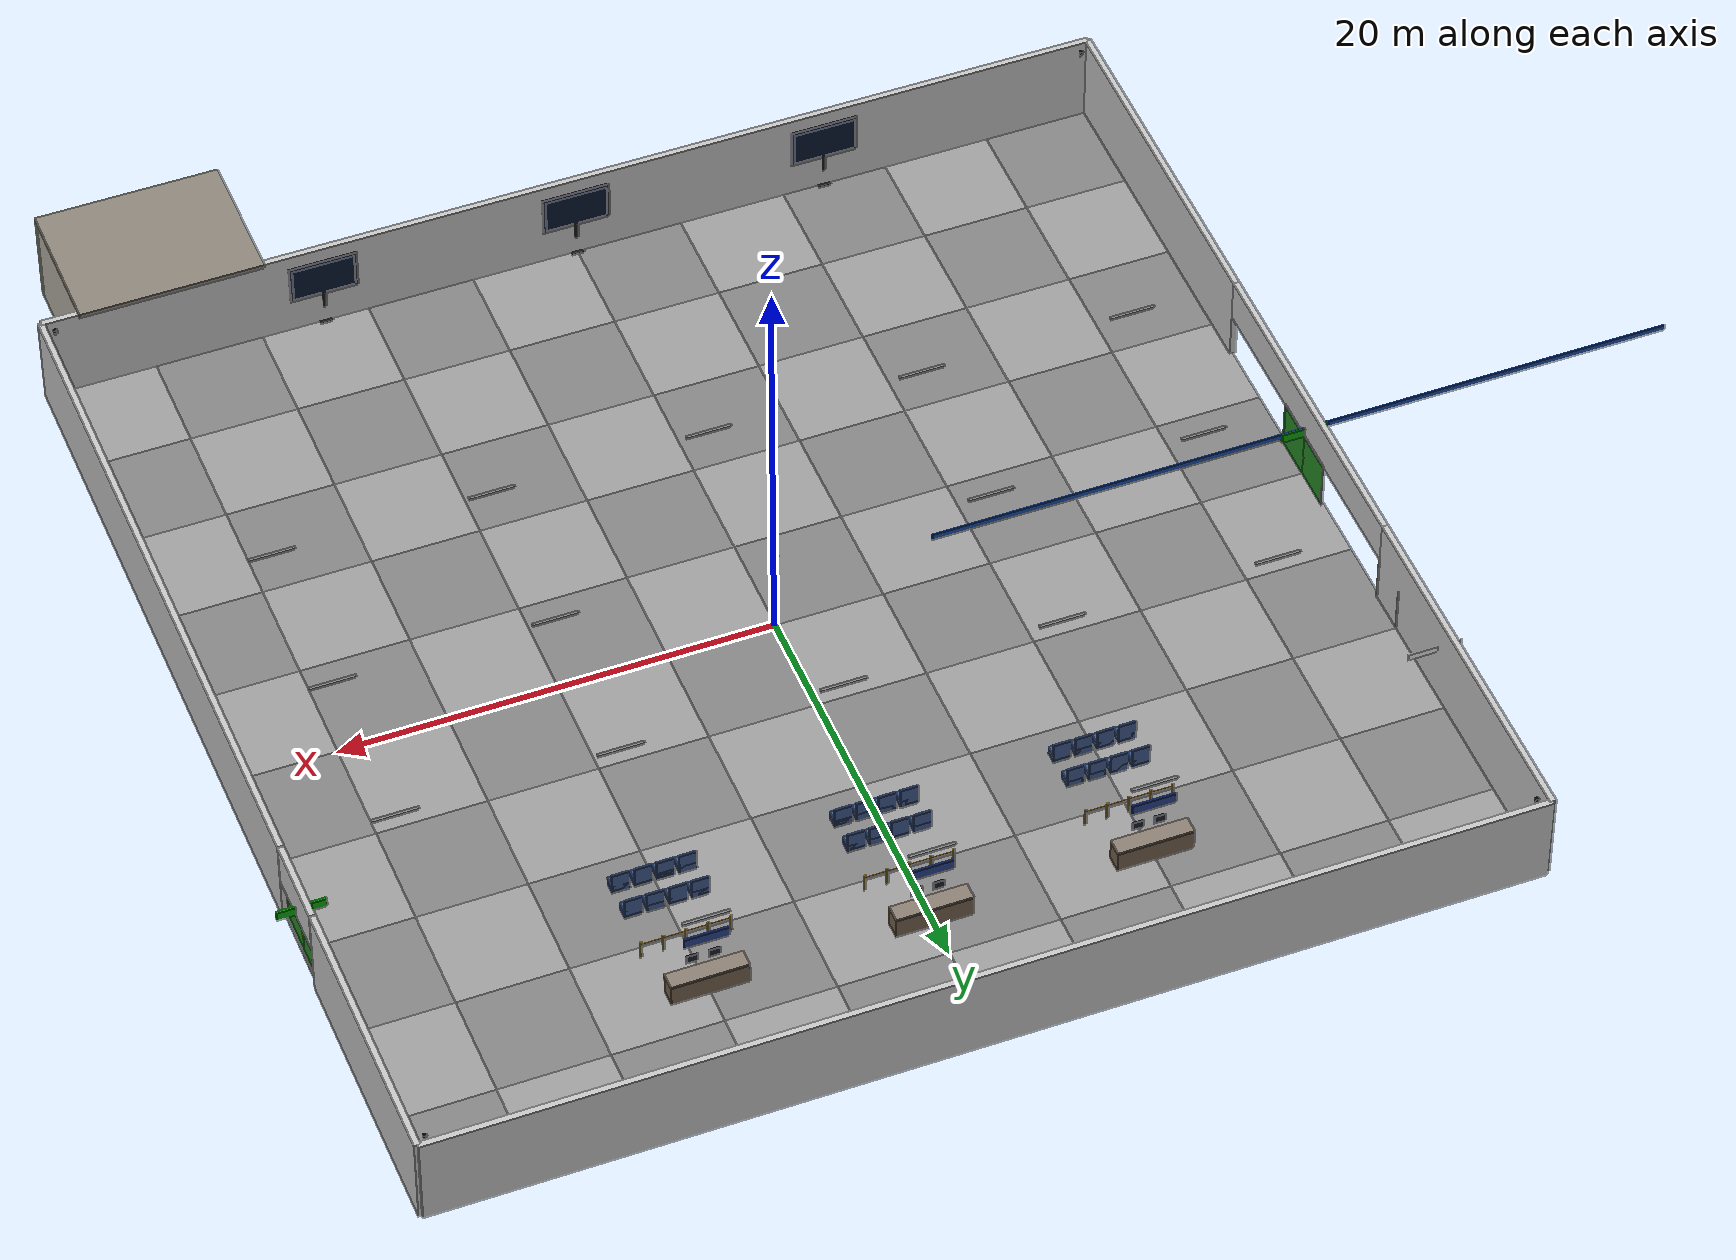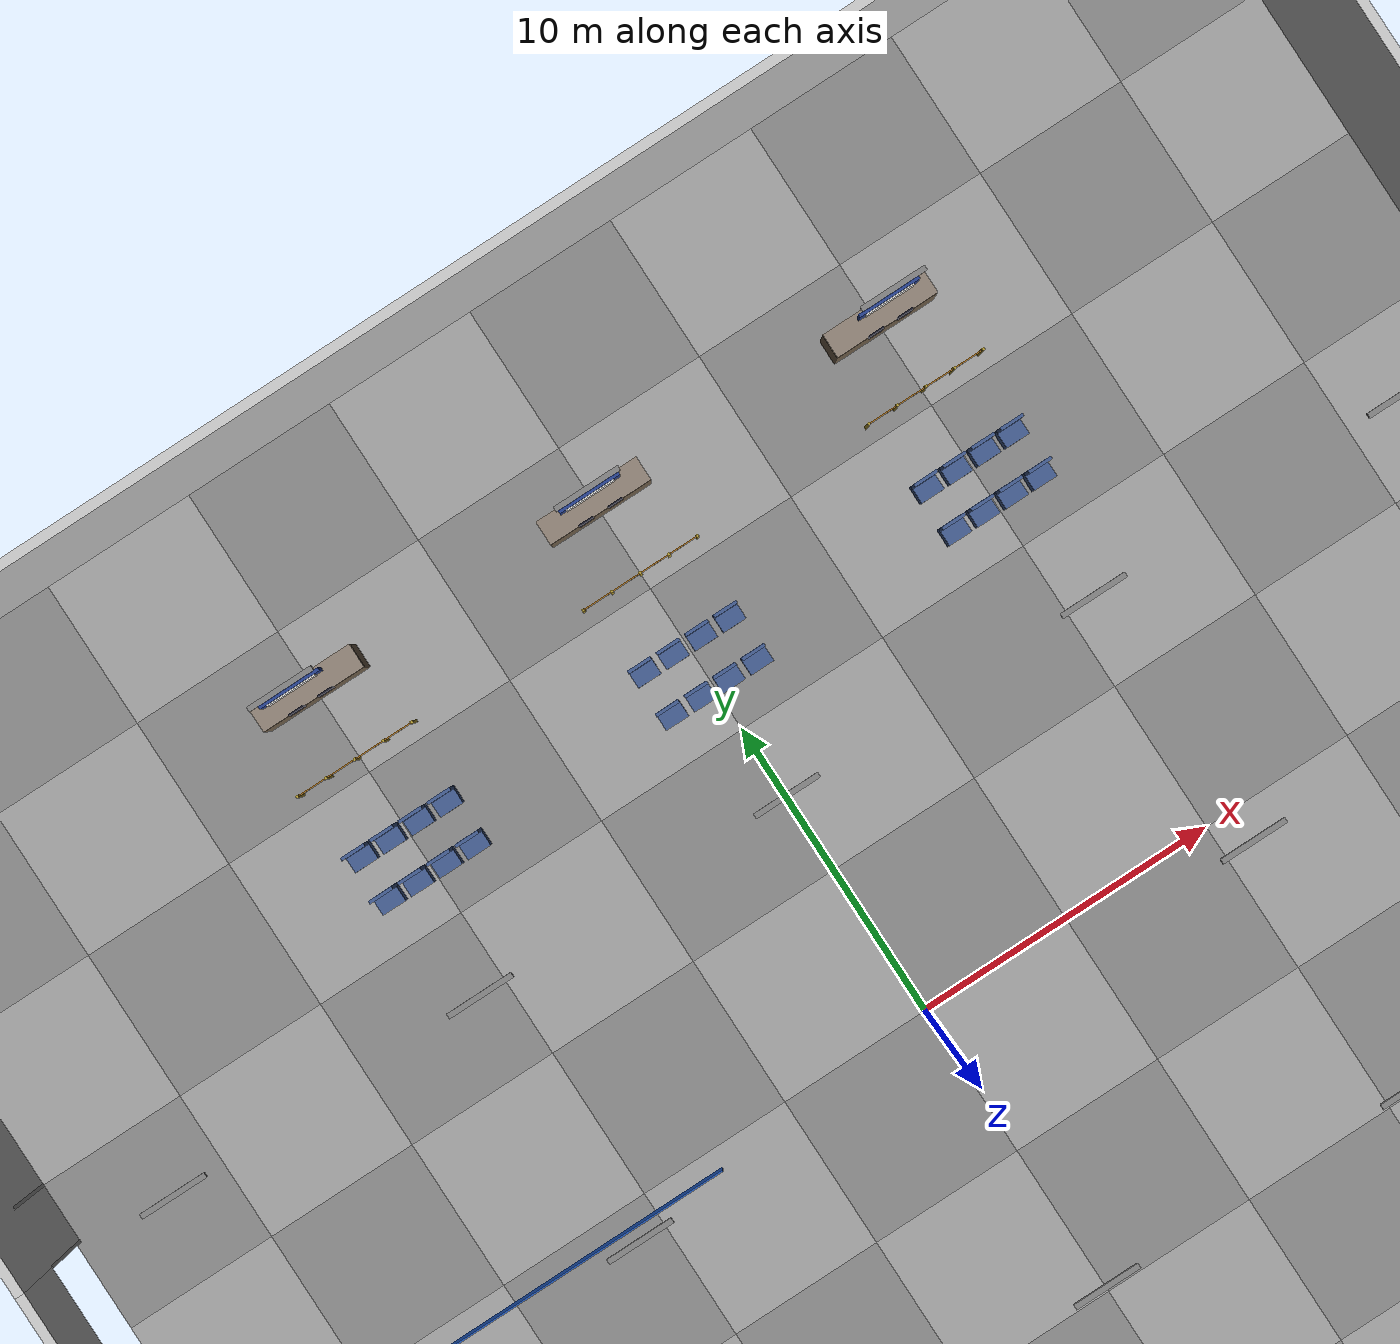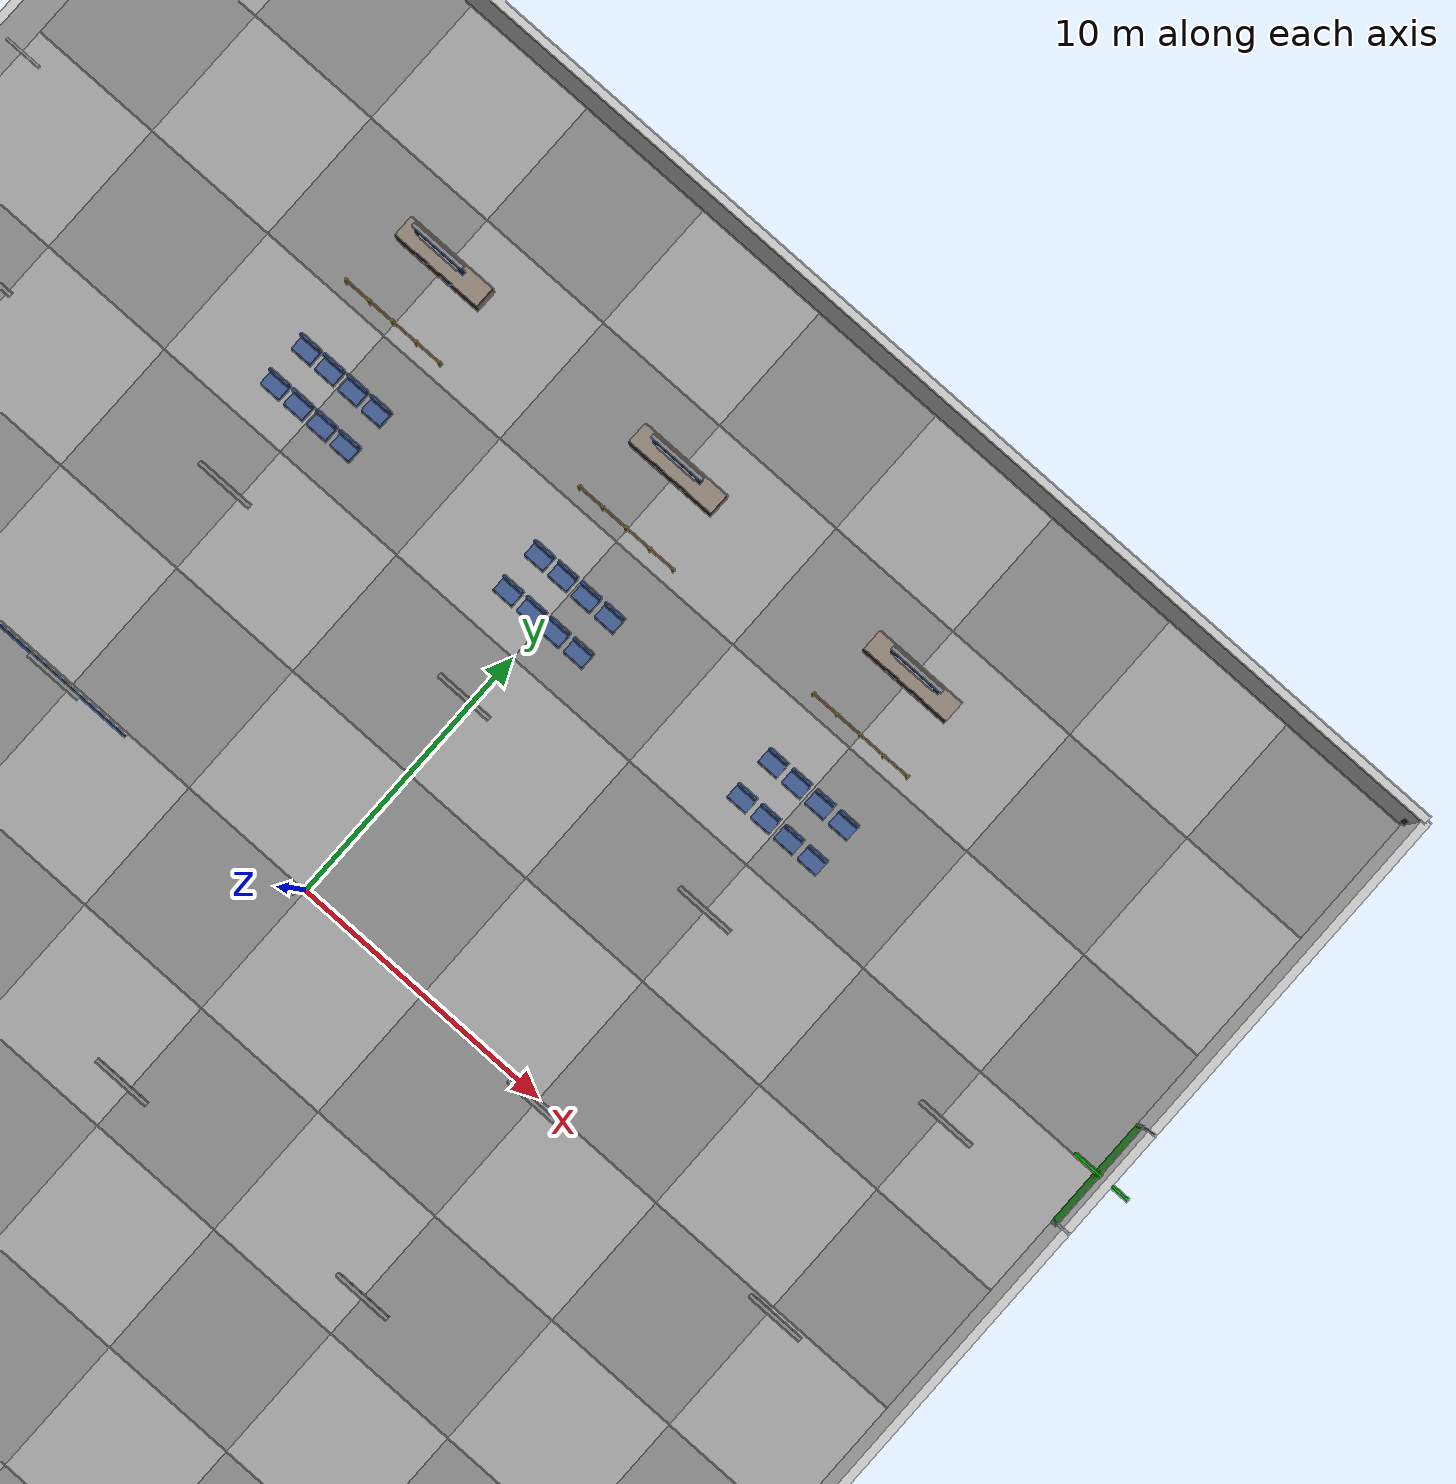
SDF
<?xml version="1.0" ?>
<sdf version="1.10">
  <world name="my_world">

  <!--  SYSTEM PLUGINS                                             -->
    <plugin filename="gz-sim-physics-system" name="gz::sim::systems::Physics"/>
    <plugin filename="gz-sim-scene-broadcaster-system" name="gz::sim::systems::SceneBroadcaster"/>
    <plugin filename="gz-sim-user-commands-system" name="gz::sim::systems::UserCommands"/>
    <plugin filename="gz-sim-contact-system" name="gz::sim::systems::Contact"/>
    <plugin filename="gz-sim-sensors-system" name="gz::sim::systems::Sensors">
      <render_engine>ogre2</render_engine>
    </plugin>

  <!--  PHYSICS                                                    -->
    <physics name="default_physics" type="ignored">
      <max_step_size>0.01</max_step_size>
      <real_time_factor>1.0</real_time_factor>
      <real_time_update_rate>100</real_time_update_rate>
    </physics>

  <!--  SCENE & LIGHTING                                           -->
    <scene>
      <ambient>0.5 0.5 0.5 1</ambient>
      <background>0.53 0.81 0.98 1</background>
      <shadows>false</shadows>
    </scene>

    <light name="light_main" type="directional">
      <pose>0 0 10 0 0 0</pose>
      <cast_shadows>false</cast_shadows>
      <diffuse>0.6 0.6 0.6 1</diffuse>
      <specular>0.1 0.1 0.1 1</specular>
      <direction>0.1 0.1 -1</direction>
      <attenuation><range>1000</range><constant>1.0</constant><linear>0.0</linear><quadratic>0.0</quadratic></attenuation>
    </light>

  <!--  FLOOR					                   -->
    <model name="tile_0_0"><static>true</static><pose>-22.5 -22.5 0.05 0 0 0</pose>
      <link name="link">
        <collision name="col"><geometry><box><size>5 5 0.1</size></box></geometry>
          <surface><friction><ode><mu>0.8</mu><mu2>0.8</mu2></ode></friction></surface></collision>
        <visual name="vis"><geometry><box><size>5 5 0.1</size></box></geometry>
          <material><ambient>0.52 0.52 0.52 1</ambient><diffuse>0.52 0.52 0.52 1</diffuse></material></visual>
      </link></model>

    <model name="tile_0_1"><static>true</static><pose>-22.5 -17.5 0.05 0 0 0</pose>
      <link name="link">
        <collision name="col"><geometry><box><size>5 5 0.1</size></box></geometry>
          <surface><friction><ode><mu>0.8</mu><mu2>0.8</mu2></ode></friction></surface></collision>
        <visual name="vis"><geometry><box><size>5 5 0.1</size></box></geometry>
          <material><ambient>0.62 0.62 0.62 1</ambient><diffuse>0.62 0.62 0.62 1</diffuse></material></visual>
      </link></model>

    <model name="tile_0_2"><static>true</static><pose>-22.5 -12.5 0.05 0 0 0</pose>
      <link name="link">
        <collision name="col"><geometry><box><size>5 5 0.1</size></box></geometry>
          <surface><friction><ode><mu>0.8</mu><mu2>0.8</mu2></ode></friction></surface></collision>
        <visual name="vis"><geometry><box><size>5 5 0.1</size></box></geometry>
          <material><ambient>0.52 0.52 0.52 1</ambient><diffuse>0.52 0.52 0.52 1</diffuse></material></visual>
      </link></model>

    <model name="tile_0_3"><static>true</static><pose>-22.5 -7.5 0.05 0 0 0</pose>
      <link name="link">
        <collision name="col"><geometry><box><size>5 5 0.1</size></box></geometry>
          <surface><friction><ode><mu>0.8</mu><mu2>0.8</mu2></ode></friction></surface></collision>
        <visual name="vis"><geometry><box><size>5 5 0.1</size></box></geometry>
          <material><ambient>0.62 0.62 0.62 1</ambient><diffuse>0.62 0.62 0.62 1</diffuse></material></visual>
      </link></model>

    <model name="tile_0_4"><static>true</static><pose>-22.5 -2.5 0.05 0 0 0</pose>
      <link name="link">
        <collision name="col"><geometry><box><size>5 5 0.1</size></box></geometry>
          <surface><friction><ode><mu>0.8</mu><mu2>0.8</mu2></ode></friction></surface></collision>
        <visual name="vis"><geometry><box><size>5 5 0.1</size></box></geometry>
          <material><ambient>0.52 0.52 0.52 1</ambient><diffuse>0.52 0.52 0.52 1</diffuse></material></visual>
      </link></model>

    <model name="tile_0_5"><static>true</static><pose>-22.5 2.5 0.05 0 0 0</pose>
      <link name="link">
        <collision name="col"><geometry><box><size>5 5 0.1</size></box></geometry>
          <surface><friction><ode><mu>0.8</mu><mu2>0.8</mu2></ode></friction></surface></collision>
        <visual name="vis"><geometry><box><size>5 5 0.1</size></box></geometry>
          <material><ambient>0.62 0.62 0.62 1</ambient><diffuse>0.62 0.62 0.62 1</diffuse></material></visual>
      </link></model>

    <model name="tile_0_6"><static>true</static><pose>-22.5 7.5 0.05 0 0 0</pose>
      <link name="link">
        <collision name="col"><geometry><box><size>5 5 0.1</size></box></geometry>
          <surface><friction><ode><mu>0.8</mu><mu2>0.8</mu2></ode></friction></surface></collision>
        <visual name="vis"><geometry><box><size>5 5 0.1</size></box></geometry>
          <material><ambient>0.52 0.52 0.52 1</ambient><diffuse>0.52 0.52 0.52 1</diffuse></material></visual>
      </link></model>

    <model name="tile_0_7"><static>true</static><pose>-22.5 12.5 0.05 0 0 0</pose>
      <link name="link">
        <collision name="col"><geometry><box><size>5 5 0.1</size></box></geometry>
          <surface><friction><ode><mu>0.8</mu><mu2>0.8</mu2></ode></friction></surface></collision>
        <visual name="vis"><geometry><box><size>5 5 0.1</size></box></geometry>
          <material><ambient>0.62 0.62 0.62 1</ambient><diffuse>0.62 0.62 0.62 1</diffuse></material></visual>
      </link></model>

    <model name="tile_0_8"><static>true</static><pose>-22.5 17.5 0.05 0 0 0</pose>
      <link name="link">
        <collision name="col"><geometry><box><size>5 5 0.1</size></box></geometry>
          <surface><friction><ode><mu>0.8</mu><mu2>0.8</mu2></ode></friction></surface></collision>
        <visual name="vis"><geometry><box><size>5 5 0.1</size></box></geometry>
          <material><ambient>0.52 0.52 0.52 1</ambient><diffuse>0.52 0.52 0.52 1</diffuse></material></visual>
      </link></model>

    <model name="tile_0_9"><static>true</static><pose>-22.5 22.5 0.05 0 0 0</pose>
      <link name="link">
        <collision name="col"><geometry><box><size>5 5 0.1</size></box></geometry>
          <surface><friction><ode><mu>0.8</mu><mu2>0.8</mu2></ode></friction></surface></collision>
        <visual name="vis"><geometry><box><size>5 5 0.1</size></box></geometry>
          <material><ambient>0.62 0.62 0.62 1</ambient><diffuse>0.62 0.62 0.62 1</diffuse></material></visual>
      </link></model>

    <model name="tile_1_0"><static>true</static><pose>-17.5 -22.5 0.05 0 0 0</pose>
      <link name="link">
        <collision name="col"><geometry><box><size>5 5 0.1</size></box></geometry>
          <surface><friction><ode><mu>0.8</mu><mu2>0.8</mu2></ode></friction></surface></collision>
        <visual name="vis"><geometry><box><size>5 5 0.1</size></box></geometry>
          <material><ambient>0.62 0.62 0.62 1</ambient><diffuse>0.62 0.62 0.62 1</diffuse></material></visual>
      </link></model>

    <model name="tile_1_1"><static>true</static><pose>-17.5 -17.5 0.05 0 0 0</pose>
      <link name="link">
        <collision name="col"><geometry><box><size>5 5 0.1</size></box></geometry>
          <surface><friction><ode><mu>0.8</mu><mu2>0.8</mu2></ode></friction></surface></collision>
        <visual name="vis"><geometry><box><size>5 5 0.1</size></box></geometry>
          <material><ambient>0.52 0.52 0.52 1</ambient><diffuse>0.52 0.52 0.52 1</diffuse></material></visual>
      </link></model>

    <model name="tile_1_2"><static>true</static><pose>-17.5 -12.5 0.05 0 0 0</pose>
      <link name="link">
        <collision name="col"><geometry><box><size>5 5 0.1</size></box></geometry>
          <surface><friction><ode><mu>0.8</mu><mu2>0.8</mu2></ode></friction></surface></collision>
        <visual name="vis"><geometry><box><size>5 5 0.1</size></box></geometry>
          <material><ambient>0.62 0.62 0.62 1</ambient><diffuse>0.62 0.62 0.62 1</diffuse></material></visual>
      </link></model>

    <model name="tile_1_3"><static>true</static><pose>-17.5 -7.5 0.05 0 0 0</pose>
      <link name="link">
        <collision name="col"><geometry><box><size>5 5 0.1</size></box></geometry>
          <surface><friction><ode><mu>0.8</mu><mu2>0.8</mu2></ode></friction></surface></collision>
        <visual name="vis"><geometry><box><size>5 5 0.1</size></box></geometry>
          <material><ambient>0.52 0.52 0.52 1</ambient><diffuse>0.52 0.52 0.52 1</diffuse></material></visual>
      </link></model>

    <model name="tile_1_4"><static>true</static><pose>-17.5 -2.5 0.05 0 0 0</pose>
      <link name="link">
        <collision name="col"><geometry><box><size>5 5 0.1</size></box></geometry>
          <surface><friction><ode><mu>0.8</mu><mu2>0.8</mu2></ode></friction></surface></collision>
        <visual name="vis"><geometry><box><size>5 5 0.1</size></box></geometry>
          <material><ambient>0.62 0.62 0.62 1</ambient><diffuse>0.62 0.62 0.62 1</diffuse></material></visual>
      </link></model>

    <model name="tile_1_5"><static>true</static><pose>-17.5 2.5 0.05 0 0 0</pose>
      <link name="link">
        <collision name="col"><geometry><box><size>5 5 0.1</size></box></geometry>
          <surface><friction><ode><mu>0.8</mu><mu2>0.8</mu2></ode></friction></surface></collision>
        <visual name="vis"><geometry><box><size>5 5 0.1</size></box></geometry>
          <material><ambient>0.52 0.52 0.52 1</ambient><diffuse>0.52 0.52 0.52 1</diffuse></material></visual>
      </link></model>

    <model name="tile_1_6"><static>true</static><pose>-17.5 7.5 0.05 0 0 0</pose>
      <link name="link">
        <collision name="col"><geometry><box><size>5 5 0.1</size></box></geometry>
          <surface><friction><ode><mu>0.8</mu><mu2>0.8</mu2></ode></friction></surface></collision>
        <visual name="vis"><geometry><box><size>5 5 0.1</size></box></geometry>
          <material><ambient>0.62 0.62 0.62 1</ambient><diffuse>0.62 0.62 0.62 1</diffuse></material></visual>
      </link></model>

    <model name="tile_1_7"><static>true</static><pose>-17.5 12.5 0.05 0 0 0</pose>
      <link name="link">
        <collision name="col"><geometry><box><size>5 5 0.1</size></box></geometry>
          <surface><friction><ode><mu>0.8</mu><mu2>0.8</mu2></ode></friction></surface></collision>
        <visual name="vis"><geometry><box><size>5 5 0.1</size></box></geometry>
          <material><ambient>0.52 0.52 0.52 1</ambient><diffuse>0.52 0.52 0.52 1</diffuse></material></visual>
      </link></model>

    <model name="tile_1_8"><static>true</static><pose>-17.5 17.5 0.05 0 0 0</pose>
      <link name="link">
        <collision name="col"><geometry><box><size>5 5 0.1</size></box></geometry>
          <surface><friction><ode><mu>0.8</mu><mu2>0.8</mu2></ode></friction></surface></collision>
        <visual name="vis"><geometry><box><size>5 5 0.1</size></box></geometry>
          <material><ambient>0.62 0.62 0.62 1</ambient><diffuse>0.62 0.62 0.62 1</diffuse></material></visual>
      </link></model>

    <model name="tile_1_9"><static>true</static><pose>-17.5 22.5 0.05 0 0 0</pose>
      <link name="link">
        <collision name="col"><geometry><box><size>5 5 0.1</size></box></geometry>
          <surface><friction><ode><mu>0.8</mu><mu2>0.8</mu2></ode></friction></surface></collision>
        <visual name="vis"><geometry><box><size>5 5 0.1</size></box></geometry>
          <material><ambient>0.52 0.52 0.52 1</ambient><diffuse>0.52 0.52 0.52 1</diffuse></material></visual>
      </link></model>

    <model name="tile_2_0"><static>true</static><pose>-12.5 -22.5 0.05 0 0 0</pose>
      <link name="link">
        <collision name="col"><geometry><box><size>5 5 0.1</size></box></geometry>
          <surface><friction><ode><mu>0.8</mu><mu2>0.8</mu2></ode></friction></surface></collision>
        <visual name="vis"><geometry><box><size>5 5 0.1</size></box></geometry>
          <material><ambient>0.52 0.52 0.52 1</ambient><diffuse>0.52 0.52 0.52 1</diffuse></material></visual>
      </link></model>

    <model name="tile_2_1"><static>true</static><pose>-12.5 -17.5 0.05 0 0 0</pose>
      <link name="link">
        <collision name="col"><geometry><box><size>5 5 0.1</size></box></geometry>
          <surface><friction><ode><mu>0.8</mu><mu2>0.8</mu2></ode></friction></surface></collision>
        <visual name="vis"><geometry><box><size>5 5 0.1</size></box></geometry>
          <material><ambient>0.62 0.62 0.62 1</ambient><diffuse>0.62 0.62 0.62 1</diffuse></material></visual>
      </link></model>

    <model name="tile_2_2"><static>true</static><pose>-12.5 -12.5 0.05 0 0 0</pose>
      <link name="link">
        <collision name="col"><geometry><box><size>5 5 0.1</size></box></geometry>
          <surface><friction><ode><mu>0.8</mu><mu2>0.8</mu2></ode></friction></surface></collision>
        <visual name="vis"><geometry><box><size>5 5 0.1</size></box></geometry>
          <material><ambient>0.52 0.52 0.52 1</ambient><diffuse>0.52 0.52 0.52 1</diffuse></material></visual>
      </link></model>

    <model name="tile_2_3"><static>true</static><pose>-12.5 -7.5 0.05 0 0 0</pose>
      <link name="link">
        <collision name="col"><geometry><box><size>5 5 0.1</size></box></geometry>
          <surface><friction><ode><mu>0.8</mu><mu2>0.8</mu2></ode></friction></surface></collision>
        <visual name="vis"><geometry><box><size>5 5 0.1</size></box></geometry>
          <material><ambient>0.62 0.62 0.62 1</ambient><diffuse>0.62 0.62 0.62 1</diffuse></material></visual>
      </link></model>

    <model name="tile_2_4"><static>true</static><pose>-12.5 -2.5 0.05 0 0 0</pose>
      <link name="link">
        <collision name="col"><geometry><box><size>5 5 0.1</size></box></geometry>
          <surface><friction><ode><mu>0.8</mu><mu2>0.8</mu2></ode></friction></surface></collision>
        <visual name="vis"><geometry><box><size>5 5 0.1</size></box></geometry>
          <material><ambient>0.52 0.52 0.52 1</ambient><diffuse>0.52 0.52 0.52 1</diffuse></material></visual>
      </link></model>

    <model name="tile_2_5"><static>true</static><pose>-12.5 2.5 0.05 0 0 0</pose>
      <link name="link">
        <collision name="col"><geometry><box><size>5 5 0.1</size></box></geometry>
          <surface><friction><ode><mu>0.8</mu><mu2>0.8</mu2></ode></friction></surface></collision>
        <visual name="vis"><geometry><box><size>5 5 0.1</size></box></geometry>
          <material><ambient>0.62 0.62 0.62 1</ambient><diffuse>0.62 0.62 0.62 1</diffuse></material></visual>
      </link></model>

    <model name="tile_2_6"><static>true</static><pose>-12.5 7.5 0.05 0 0 0</pose>
      <link name="link">
        <collision name="col"><geometry><box><size>5 5 0.1</size></box></geometry>
          <surface><friction><ode><mu>0.8</mu><mu2>0.8</mu2></ode></friction></surface></collision>
        <visual name="vis"><geometry><box><size>5 5 0.1</size></box></geometry>
          <material><ambient>0.52 0.52 0.52 1</ambient><diffuse>0.52 0.52 0.52 1</diffuse></material></visual>
      </link></model>

    <model name="tile_2_7"><static>true</static><pose>-12.5 12.5 0.05 0 0 0</pose>
      <link name="link">
        <collision name="col"><geometry><box><size>5 5 0.1</size></box></geometry>
          <surface><friction><ode><mu>0.8</mu><mu2>0.8</mu2></ode></friction></surface></collision>
        <visual name="vis"><geometry><box><size>5 5 0.1</size></box></geometry>
          <material><ambient>0.62 0.62 0.62 1</ambient><diffuse>0.62 0.62 0.62 1</diffuse></material></visual>
      </link></model>

    <model name="tile_2_8"><static>true</static><pose>-12.5 17.5 0.05 0 0 0</pose>
      <link name="link">
        <collision name="col"><geometry><box><size>5 5 0.1</size></box></geometry>
          <surface><friction><ode><mu>0.8</mu><mu2>0.8</mu2></ode></friction></surface></collision>
        <visual name="vis"><geometry><box><size>5 5 0.1</size></box></geometry>
          <material><ambient>0.52 0.52 0.52 1</ambient><diffuse>0.52 0.52 0.52 1</diffuse></material></visual>
      </link></model>

    <model name="tile_2_9"><static>true</static><pose>-12.5 22.5 0.05 0 0 0</pose>
      <link name="link">
        <collision name="col"><geometry><box><size>5 5 0.1</size></box></geometry>
          <surface><friction><ode><mu>0.8</mu><mu2>0.8</mu2></ode></friction></surface></collision>
        <visual name="vis"><geometry><box><size>5 5 0.1</size></box></geometry>
          <material><ambient>0.62 0.62 0.62 1</ambient><diffuse>0.62 0.62 0.62 1</diffuse></material></visual>
      </link></model>

    <model name="tile_3_0"><static>true</static><pose>-7.5 -22.5 0.05 0 0 0</pose>
      <link name="link">
        <collision name="col"><geometry><box><size>5 5 0.1</size></box></geometry>
          <surface><friction><ode><mu>0.8</mu><mu2>0.8</mu2></ode></friction></surface></collision>
        <visual name="vis"><geometry><box><size>5 5 0.1</size></box></geometry>
          <material><ambient>0.62 0.62 0.62 1</ambient><diffuse>0.62 0.62 0.62 1</diffuse></material></visual>
      </link></model>

    <model name="tile_3_1"><static>true</static><pose>-7.5 -17.5 0.05 0 0 0</pose>
      <link name="link">
        <collision name="col"><geometry><box><size>5 5 0.1</size></box></geometry>
          <surface><friction><ode><mu>0.8</mu><mu2>0.8</mu2></ode></friction></surface></collision>
        <visual name="vis"><geometry><box><size>5 5 0.1</size></box></geometry>
          <material><ambient>0.52 0.52 0.52 1</ambient><diffuse>0.52 0.52 0.52 1</diffuse></material></visual>
      </link></model>

    <model name="tile_3_2"><static>true</static><pose>-7.5 -12.5 0.05 0 0 0</pose>
      <link name="link">
        <collision name="col"><geometry><box><size>5 5 0.1</size></box></geometry>
          <surface><friction><ode><mu>0.8</mu><mu2>0.8</mu2></ode></friction></surface></collision>
        <visual name="vis"><geometry><box><size>5 5 0.1</size></box></geometry>
          <material><ambient>0.62 0.62 0.62 1</ambient><diffuse>0.62 0.62 0.62 1</diffuse></material></visual>
      </link></model>

    <model name="tile_3_3"><static>true</static><pose>-7.5 -7.5 0.05 0 0 0</pose>
      <link name="link">
        <collision name="col"><geometry><box><size>5 5 0.1</size></box></geometry>
          <surface><friction><ode><mu>0.8</mu><mu2>0.8</mu2></ode></friction></surface></collision>
        <visual name="vis"><geometry><box><size>5 5 0.1</size></box></geometry>
          <material><ambient>0.52 0.52 0.52 1</ambient><diffuse>0.52 0.52 0.52 1</diffuse></material></visual>
      </link></model>

    <model name="tile_3_4"><static>true</static><pose>-7.5 -2.5 0.05 0 0 0</pose>
      <link name="link">
        <collision name="col"><geometry><box><size>5 5 0.1</size></box></geometry>
          <surface><friction><ode><mu>0.8</mu><mu2>0.8</mu2></ode></friction></surface></collision>
        <visual name="vis"><geometry><box><size>5 5 0.1</size></box></geometry>
          <material><ambient>0.62 0.62 0.62 1</ambient><diffuse>0.62 0.62 0.62 1</diffuse></material></visual>
      </link></model>

    <model name="tile_3_5"><static>true</static><pose>-7.5 2.5 0.05 0 0 0</pose>
      <link name="link">
        <collision name="col"><geometry><box><size>5 5 0.1</size></box></geometry>
          <surface><friction><ode><mu>0.8</mu><mu2>0.8</mu2></ode></friction></surface></collision>
        <visual name="vis"><geometry><box><size>5 5 0.1</size></box></geometry>
          <material><ambient>0.52 0.52 0.52 1</ambient><diffuse>0.52 0.52 0.52 1</diffuse></material></visual>
      </link></model>

    <model name="tile_3_6"><static>true</static><pose>-7.5 7.5 0.05 0 0 0</pose>
      <link name="link">
        <collision name="col"><geometry><box><size>5 5 0.1</size></box></geometry>
          <surface><friction><ode><mu>0.8</mu><mu2>0.8</mu2></ode></friction></surface></collision>
        <visual name="vis"><geometry><box><size>5 5 0.1</size></box></geometry>
          <material><ambient>0.62 0.62 0.62 1</ambient><diffuse>0.62 0.62 0.62 1</diffuse></material></visual>
      </link></model>

    <model name="tile_3_7"><static>true</static><pose>-7.5 12.5 0.05 0 0 0</pose>
      <link name="link">
        <collision name="col"><geometry><box><size>5 5 0.1</size></box></geometry>
          <surface><friction><ode><mu>0.8</mu><mu2>0.8</mu2></ode></friction></surface></collision>
        <visual name="vis"><geometry><box><size>5 5 0.1</size></box></geometry>
          <material><ambient>0.52 0.52 0.52 1</ambient><diffuse>0.52 0.52 0.52 1</diffuse></material></visual>
      </link></model>

    <model name="tile_3_8"><static>true</static><pose>-7.5 17.5 0.05 0 0 0</pose>
      <link name="link">
        <collision name="col"><geometry><box><size>5 5 0.1</size></box></geometry>
          <surface><friction><ode><mu>0.8</mu><mu2>0.8</mu2></ode></friction></surface></collision>
        <visual name="vis"><geometry><box><size>5 5 0.1</size></box></geometry>
          <material><ambient>0.62 0.62 0.62 1</ambient><diffuse>0.62 0.62 0.62 1</diffuse></material></visual>
      </link></model>

    <model name="tile_3_9"><static>true</static><pose>-7.5 22.5 0.05 0 0 0</pose>
      <link name="link">
        <collision name="col"><geometry><box><size>5 5 0.1</size></box></geometry>
          <surface><friction><ode><mu>0.8</mu><mu2>0.8</mu2></ode></friction></surface></collision>
        <visual name="vis"><geometry><box><size>5 5 0.1</size></box></geometry>
          <material><ambient>0.52 0.52 0.52 1</ambient><diffuse>0.52 0.52 0.52 1</diffuse></material></visual>
      </link></model>

    <model name="tile_4_0"><static>true</static><pose>-2.5 -22.5 0.05 0 0 0</pose>
      <link name="link">
        <collision name="col"><geometry><box><size>5 5 0.1</size></box></geometry>
          <surface><friction><ode><mu>0.8</mu><mu2>0.8</mu2></ode></friction></surface></collision>
        <visual name="vis"><geometry><box><size>5 5 0.1</size></box></geometry>
          <material><ambient>0.52 0.52 0.52 1</ambient><diffuse>0.52 0.52 0.52 1</diffuse></material></visual>
      </link></model>

    <model name="tile_4_1"><static>true</static><pose>-2.5 -17.5 0.05 0 0 0</pose>
      <link name="link">
        <collision name="col"><geometry><box><size>5 5 0.1</size></box></geometry>
          <surface><friction><ode><mu>0.8</mu><mu2>0.8</mu2></ode></friction></surface></collision>
        <visual name="vis"><geometry><box><size>5 5 0.1</size></box></geometry>
          <material><ambient>0.62 0.62 0.62 1</ambient><diffuse>0.62 0.62 0.62 1</diffuse></material></visual>
      </link></model>

    <model name="tile_4_2"><static>true</static><pose>-2.5 -12.5 0.05 0 0 0</pose>
      <link name="link">
        <collision name="col"><geometry><box><size>5 5 0.1</size></box></geometry>
          <surface><friction><ode><mu>0.8</mu><mu2>0.8</mu2></ode></friction></surface></collision>
        <visual name="vis"><geometry><box><size>5 5 0.1</size></box></geometry>
          <material><ambient>0.52 0.52 0.52 1</ambient><diffuse>0.52 0.52 0.52 1</diffuse></material></visual>
      </link></model>

    <model name="tile_4_3"><static>true</static><pose>-2.5 -7.5 0.05 0 0 0</pose>
      <link name="link">
        <collision name="col"><geometry><box><size>5 5 0.1</size></box></geometry>
          <surface><friction><ode><mu>0.8</mu><mu2>0.8</mu2></ode></friction></surface></collision>
        <visual name="vis"><geometry><box><size>5 5 0.1</size></box></geometry>
          <material><ambient>0.62 0.62 0.62 1</ambient><diffuse>0.62 0.62 0.62 1</diffuse></material></visual>
      </link></model>

    <model name="tile_4_4"><static>true</static><pose>-2.5 -2.5 0.05 0 0 0</pose>
      <link name="link">
        <collision name="col"><geometry><box><size>5 5 0.1</size></box></geometry>
          <surface><friction><ode><mu>0.8</mu><mu2>0.8</mu2></ode></friction></surface></collision>
        <visual name="vis"><geometry><box><size>5 5 0.1</size></box></geometry>
          <material><ambient>0.52 0.52 0.52 1</ambient><diffuse>0.52 0.52 0.52 1</diffuse></material></visual>
      </link></model>

    <model name="tile_4_5"><static>true</static><pose>-2.5 2.5 0.05 0 0 0</pose>
      <link name="link">
        <collision name="col"><geometry><box><size>5 5 0.1</size></box></geometry>
          <surface><friction><ode><mu>0.8</mu><mu2>0.8</mu2></ode></friction></surface></collision>
        <visual name="vis"><geometry><box><size>5 5 0.1</size></box></geometry>
          <material><ambient>0.62 0.62 0.62 1</ambient><diffuse>0.62 0.62 0.62 1</diffuse></material></visual>
      </link></model>

    <model name="tile_4_6"><static>true</static><pose>-2.5 7.5 0.05 0 0 0</pose>
      <link name="link">
        <collision name="col"><geometry><box><size>5 5 0.1</size></box></geometry>
          <surface><friction><ode><mu>0.8</mu><mu2>0.8</mu2></ode></friction></surface></collision>
        <visual name="vis"><geometry><box><size>5 5 0.1</size></box></geometry>
          <material><ambient>0.52 0.52 0.52 1</ambient><diffuse>0.52 0.52 0.52 1</diffuse></material></visual>
      </link></model>

    <model name="tile_4_7"><static>true</static><pose>-2.5 12.5 0.05 0 0 0</pose>
      <link name="link">
        <collision name="col"><geometry><box><size>5 5 0.1</size></box></geometry>
          <surface><friction><ode><mu>0.8</mu><mu2>0.8</mu2></ode></friction></surface></collision>
        <visual name="vis"><geometry><box><size>5 5 0.1</size></box></geometry>
          <material><ambient>0.62 0.62 0.62 1</ambient><diffuse>0.62 0.62 0.62 1</diffuse></material></visual>
      </link></model>

    <model name="tile_4_8"><static>true</static><pose>-2.5 17.5 0.05 0 0 0</pose>
      <link name="link">
        <collision name="col"><geometry><box><size>5 5 0.1</size></box></geometry>
          <surface><friction><ode><mu>0.8</mu><mu2>0.8</mu2></ode></friction></surface></collision>
        <visual name="vis"><geometry><box><size>5 5 0.1</size></box></geometry>
          <material><ambient>0.52 0.52 0.52 1</ambient><diffuse>0.52 0.52 0.52 1</diffuse></material></visual>
      </link></model>

    <model name="tile_4_9"><static>true</static><pose>-2.5 22.5 0.05 0 0 0</pose>
      <link name="link">
        <collision name="col"><geometry><box><size>5 5 0.1</size></box></geometry>
          <surface><friction><ode><mu>0.8</mu><mu2>0.8</mu2></ode></friction></surface></collision>
        <visual name="vis"><geometry><box><size>5 5 0.1</size></box></geometry>
          <material><ambient>0.62 0.62 0.62 1</ambient><diffuse>0.62 0.62 0.62 1</diffuse></material></visual>
      </link></model>

    <model name="tile_5_0"><static>true</static><pose>2.5 -22.5 0.05 0 0 0</pose>
      <link name="link">
        <collision name="col"><geometry><box><size>5 5 0.1</size></box></geometry>
          <surface><friction><ode><mu>0.8</mu><mu2>0.8</mu2></ode></friction></surface></collision>
        <visual name="vis"><geometry><box><size>5 5 0.1</size></box></geometry>
          <material><ambient>0.62 0.62 0.62 1</ambient><diffuse>0.62 0.62 0.62 1</diffuse></material></visual>
      </link></model>

    <model name="tile_5_1"><static>true</static><pose>2.5 -17.5 0.05 0 0 0</pose>
      <link name="link">
        <collision name="col"><geometry><box><size>5 5 0.1</size></box></geometry>
          <surface><friction><ode><mu>0.8</mu><mu2>0.8</mu2></ode></friction></surface></collision>
        <visual name="vis"><geometry><box><size>5 5 0.1</size></box></geometry>
          <material><ambient>0.52 0.52 0.52 1</ambient><diffuse>0.52 0.52 0.52 1</diffuse></material></visual>
      </link></model>

    <model name="tile_5_2"><static>true</static><pose>2.5 -12.5 0.05 0 0 0</pose>
      <link name="link">
        <collision name="col"><geometry><box><size>5 5 0.1</size></box></geometry>
          <surface><friction><ode><mu>0.8</mu><mu2>0.8</mu2></ode></friction></surface></collision>
        <visual name="vis"><geometry><box><size>5 5 0.1</size></box></geometry>
          <material><ambient>0.62 0.62 0.62 1</ambient><diffuse>0.62 0.62 0.62 1</diffuse></material></visual>
      </link></model>

    <model name="tile_5_3"><static>true</static><pose>2.5 -7.5 0.05 0 0 0</pose>
      <link name="link">
        <collision name="col"><geometry><box><size>5 5 0.1</size></box></geometry>
          <surface><friction><ode><mu>0.8</mu><mu2>0.8</mu2></ode></friction></surface></collision>
        <visual name="vis"><geometry><box><size>5 5 0.1</size></box></geometry>
          <material><ambient>0.52 0.52 0.52 1</ambient><diffuse>0.52 0.52 0.52 1</diffuse></material></visual>
      </link></model>

    <model name="tile_5_4"><static>true</static><pose>2.5 -2.5 0.05 0 0 0</pose>
      <link name="link">
        <collision name="col"><geometry><box><size>5 5 0.1</size></box></geometry>
          <surface><friction><ode><mu>0.8</mu><mu2>0.8</mu2></ode></friction></surface></collision>
        <visual name="vis"><geometry><box><size>5 5 0.1</size></box></geometry>
          <material><ambient>0.62 0.62 0.62 1</ambient><diffuse>0.62 0.62 0.62 1</diffuse></material></visual>
      </link></model>

    <model name="tile_5_5"><static>true</static><pose>2.5 2.5 0.05 0 0 0</pose>
      <link name="link">
        <collision name="col"><geometry><box><size>5 5 0.1</size></box></geometry>
          <surface><friction><ode><mu>0.8</mu><mu2>0.8</mu2></ode></friction></surface></collision>
        <visual name="vis"><geometry><box><size>5 5 0.1</size></box></geometry>
          <material><ambient>0.52 0.52 0.52 1</ambient><diffuse>0.52 0.52 0.52 1</diffuse></material></visual>
      </link></model>

    <model name="tile_5_6"><static>true</static><pose>2.5 7.5 0.05 0 0 0</pose>
      <link name="link">
        <collision name="col"><geometry><box><size>5 5 0.1</size></box></geometry>
          <surface><friction><ode><mu>0.8</mu><mu2>0.8</mu2></ode></friction></surface></collision>
        <visual name="vis"><geometry><box><size>5 5 0.1</size></box></geometry>
          <material><ambient>0.62 0.62 0.62 1</ambient><diffuse>0.62 0.62 0.62 1</diffuse></material></visual>
      </link></model>

    <model name="tile_5_7"><static>true</static><pose>2.5 12.5 0.05 0 0 0</pose>
      <link name="link">
        <collision name="col"><geometry><box><size>5 5 0.1</size></box></geometry>
          <surface><friction><ode><mu>0.8</mu><mu2>0.8</mu2></ode></friction></surface></collision>
        <visual name="vis"><geometry><box><size>5 5 0.1</size></box></geometry>
          <material><ambient>0.52 0.52 0.52 1</ambient><diffuse>0.52 0.52 0.52 1</diffuse></material></visual>
      </link></model>

    <model name="tile_5_8"><static>true</static><pose>2.5 17.5 0.05 0 0 0</pose>
      <link name="link">
        <collision name="col"><geometry><box><size>5 5 0.1</size></box></geometry>
          <surface><friction><ode><mu>0.8</mu><mu2>0.8</mu2></ode></friction></surface></collision>
        <visual name="vis"><geometry><box><size>5 5 0.1</size></box></geometry>
          <material><ambient>0.62 0.62 0.62 1</ambient><diffuse>0.62 0.62 0.62 1</diffuse></material></visual>
      </link></model>

    <model name="tile_5_9"><static>true</static><pose>2.5 22.5 0.05 0 0 0</pose>
      <link name="link">
        <collision name="col"><geometry><box><size>5 5 0.1</size></box></geometry>
          <surface><friction><ode><mu>0.8</mu><mu2>0.8</mu2></ode></friction></surface></collision>
        <visual name="vis"><geometry><box><size>5 5 0.1</size></box></geometry>
          <material><ambient>0.52 0.52 0.52 1</ambient><diffuse>0.52 0.52 0.52 1</diffuse></material></visual>
      </link></model>

    <model name="tile_6_0"><static>true</static><pose>7.5 -22.5 0.05 0 0 0</pose>
      <link name="link">
        <collision name="col"><geometry><box><size>5 5 0.1</size></box></geometry>
          <surface><friction><ode><mu>0.8</mu><mu2>0.8</mu2></ode></friction></surface></collision>
        <visual name="vis"><geometry><box><size>5 5 0.1</size></box></geometry>
          <material><ambient>0.52 0.52 0.52 1</ambient><diffuse>0.52 0.52 0.52 1</diffuse></material></visual>
      </link></model>

    <model name="tile_6_1"><static>true</static><pose>7.5 -17.5 0.05 0 0 0</pose>
      <link name="link">
        <collision name="col"><geometry><box><size>5 5 0.1</size></box></geometry>
          <surface><friction><ode><mu>0.8</mu><mu2>0.8</mu2></ode></friction></surface></collision>
        <visual name="vis"><geometry><box><size>5 5 0.1</size></box></geometry>
          <material><ambient>0.62 0.62 0.62 1</ambient><diffuse>0.62 0.62 0.62 1</diffuse></material></visual>
      </link></model>

    <model name="tile_6_2"><static>true</static><pose>7.5 -12.5 0.05 0 0 0</pose>
      <link name="link">
        <collision name="col"><geometry><box><size>5 5 0.1</size></box></geometry>
          <surface><friction><ode><mu>0.8</mu><mu2>0.8</mu2></ode></friction></surface></collision>
        <visual name="vis"><geometry><box><size>5 5 0.1</size></box></geometry>
          <material><ambient>0.52 0.52 0.52 1</ambient><diffuse>0.52 0.52 0.52 1</diffuse></material></visual>
      </link></model>

    <model name="tile_6_3"><static>true</static><pose>7.5 -7.5 0.05 0 0 0</pose>
      <link name="link">
        <collision name="col"><geometry><box><size>5 5 0.1</size></box></geometry>
          <surface><friction><ode><mu>0.8</mu><mu2>0.8</mu2></ode></friction></surface></collision>
        <visual name="vis"><geometry><box><size>5 5 0.1</size></box></geometry>
          <material><ambient>0.62 0.62 0.62 1</ambient><diffuse>0.62 0.62 0.62 1</diffuse></material></visual>
      </link></model>

    <model name="tile_6_4"><static>true</static><pose>7.5 -2.5 0.05 0 0 0</pose>
      <link name="link">
        <collision name="col"><geometry><box><size>5 5 0.1</size></box></geometry>
          <surface><friction><ode><mu>0.8</mu><mu2>0.8</mu2></ode></friction></surface></collision>
        <visual name="vis"><geometry><box><size>5 5 0.1</size></box></geometry>
          <material><ambient>0.52 0.52 0.52 1</ambient><diffuse>0.52 0.52 0.52 1</diffuse></material></visual>
      </link></model>

    <model name="tile_6_5"><static>true</static><pose>7.5 2.5 0.05 0 0 0</pose>
      <link name="link">
        <collision name="col"><geometry><box><size>5 5 0.1</size></box></geometry>
          <surface><friction><ode><mu>0.8</mu><mu2>0.8</mu2></ode></friction></surface></collision>
        <visual name="vis"><geometry><box><size>5 5 0.1</size></box></geometry>
          <material><ambient>0.62 0.62 0.62 1</ambient><diffuse>0.62 0.62 0.62 1</diffuse></material></visual>
      </link></model>

    <model name="tile_6_6"><static>true</static><pose>7.5 7.5 0.05 0 0 0</pose>
      <link name="link">
        <collision name="col"><geometry><box><size>5 5 0.1</size></box></geometry>
          <surface><friction><ode><mu>0.8</mu><mu2>0.8</mu2></ode></friction></surface></collision>
        <visual name="vis"><geometry><box><size>5 5 0.1</size></box></geometry>
          <material><ambient>0.52 0.52 0.52 1</ambient><diffuse>0.52 0.52 0.52 1</diffuse></material></visual>
      </link></model>

    <model name="tile_6_7"><static>true</static><pose>7.5 12.5 0.05 0 0 0</pose>
      <link name="link">
        <collision name="col"><geometry><box><size>5 5 0.1</size></box></geometry>
          <surface><friction><ode><mu>0.8</mu><mu2>0.8</mu2></ode></friction></surface></collision>
        <visual name="vis"><geometry><box><size>5 5 0.1</size></box></geometry>
          <material><ambient>0.62 0.62 0.62 1</ambient><diffuse>0.62 0.62 0.62 1</diffuse></material></visual>
      </link></model>

    <model name="tile_6_8"><static>true</static><pose>7.5 17.5 0.05 0 0 0</pose>
      <link name="link">
        <collision name="col"><geometry><box><size>5 5 0.1</size></box></geometry>
          <surface><friction><ode><mu>0.8</mu><mu2>0.8</mu2></ode></friction></surface></collision>
        <visual name="vis"><geometry><box><size>5 5 0.1</size></box></geometry>
          <material><ambient>0.52 0.52 0.52 1</ambient><diffuse>0.52 0.52 0.52 1</diffuse></material></visual>
      </link></model>

    <model name="tile_6_9"><static>true</static><pose>7.5 22.5 0.05 0 0 0</pose>
      <link name="link">
        <collision name="col"><geometry><box><size>5 5 0.1</size></box></geometry>
          <surface><friction><ode><mu>0.8</mu><mu2>0.8</mu2></ode></friction></surface></collision>
        <visual name="vis"><geometry><box><size>5 5 0.1</size></box></geometry>
          <material><ambient>0.62 0.62 0.62 1</ambient><diffuse>0.62 0.62 0.62 1</diffuse></material></visual>
      </link></model>

    <model name="tile_7_0"><static>true</static><pose>12.5 -22.5 0.05 0 0 0</pose>
      <link name="link">
        <collision name="col"><geometry><box><size>5 5 0.1</size></box></geometry>
          <surface><friction><ode><mu>0.8</mu><mu2>0.8</mu2></ode></friction></surface></collision>
        <visual name="vis"><geometry><box><size>5 5 0.1</size></box></geometry>
          <material><ambient>0.62 0.62 0.62 1</ambient><diffuse>0.62 0.62 0.62 1</diffuse></material></visual>
      </link></model>

    <model name="tile_7_1"><static>true</static><pose>12.5 -17.5 0.05 0 0 0</pose>
      <link name="link">
        <collision name="col"><geometry><box><size>5 5 0.1</size></box></geometry>
          <surface><friction><ode><mu>0.8</mu><mu2>0.8</mu2></ode></friction></surface></collision>
        <visual name="vis"><geometry><box><size>5 5 0.1</size></box></geometry>
          <material><ambient>0.52 0.52 0.52 1</ambient><diffuse>0.52 0.52 0.52 1</diffuse></material></visual>
      </link></model>

    <model name="tile_7_2"><static>true</static><pose>12.5 -12.5 0.05 0 0 0</pose>
      <link name="link">
        <collision name="col"><geometry><box><size>5 5 0.1</size></box></geometry>
          <surface><friction><ode><mu>0.8</mu><mu2>0.8</mu2></ode></friction></surface></collision>
        <visual name="vis"><geometry><box><size>5 5 0.1</size></box></geometry>
          <material><ambient>0.62 0.62 0.62 1</ambient><diffuse>0.62 0.62 0.62 1</diffuse></material></visual>
      </link></model>

    <model name="tile_7_3"><static>true</static><pose>12.5 -7.5 0.05 0 0 0</pose>
      <link name="link">
        <collision name="col"><geometry><box><size>5 5 0.1</size></box></geometry>
          <surface><friction><ode><mu>0.8</mu><mu2>0.8</mu2></ode></friction></surface></collision>
        <visual name="vis"><geometry><box><size>5 5 0.1</size></box></geometry>
          <material><ambient>0.52 0.52 0.52 1</ambient><diffuse>0.52 0.52 0.52 1</diffuse></material></visual>
      </link></model>

    <model name="tile_7_4"><static>true</static><pose>12.5 -2.5 0.05 0 0 0</pose>
      <link name="link">
        <collision name="col"><geometry><box><size>5 5 0.1</size></box></geometry>
          <surface><friction><ode><mu>0.8</mu><mu2>0.8</mu2></ode></friction></surface></collision>
        <visual name="vis"><geometry><box><size>5 5 0.1</size></box></geometry>
          <material><ambient>0.62 0.62 0.62 1</ambient><diffuse>0.62 0.62 0.62 1</diffuse></material></visual>
      </link></model>

    <model name="tile_7_5"><static>true</static><pose>12.5 2.5 0.05 0 0 0</pose>
      <link name="link">
        <collision name="col"><geometry><box><size>5 5 0.1</size></box></geometry>
          <surface><friction><ode><mu>0.8</mu><mu2>0.8</mu2></ode></friction></surface></collision>
        <visual name="vis"><geometry><box><size>5 5 0.1</size></box></geometry>
          <material><ambient>0.52 0.52 0.52 1</ambient><diffuse>0.52 0.52 0.52 1</diffuse></material></visual>
      </link></model>

    <model name="tile_7_6"><static>true</static><pose>12.5 7.5 0.05 0 0 0</pose>
      <link name="link">
        <collision name="col"><geometry><box><size>5 5 0.1</size></box></geometry>
          <surface><friction><ode><mu>0.8</mu><mu2>0.8</mu2></ode></friction></surface></collision>
        <visual name="vis"><geometry><box><size>5 5 0.1</size></box></geometry>
          <material><ambient>0.62 0.62 0.62 1</ambient><diffuse>0.62 0.62 0.62 1</diffuse></material></visual>
      </link></model>

    <model name="tile_7_7"><static>true</static><pose>12.5 12.5 0.05 0 0 0</pose>
      <link name="link">
        <collision name="col"><geometry><box><size>5 5 0.1</size></box></geometry>
          <surface><friction><ode><mu>0.8</mu><mu2>0.8</mu2></ode></friction></surface></collision>
        <visual name="vis"><geometry><box><size>5 5 0.1</size></box></geometry>
          <material><ambient>0.52 0.52 0.52 1</ambient><diffuse>0.52 0.52 0.52 1</diffuse></material></visual>
      </link></model>

    <model name="tile_7_8"><static>true</static><pose>12.5 17.5 0.05 0 0 0</pose>
      <link name="link">
        <collision name="col"><geometry><box><size>5 5 0.1</size></box></geometry>
          <surface><friction><ode><mu>0.8</mu><mu2>0.8</mu2></ode></friction></surface></collision>
        <visual name="vis"><geometry><box><size>5 5 0.1</size></box></geometry>
          <material><ambient>0.62 0.62 0.62 1</ambient><diffuse>0.62 0.62 0.62 1</diffuse></material></visual>
      </link></model>

    <model name="tile_7_9"><static>true</static><pose>12.5 22.5 0.05 0 0 0</pose>
      <link name="link">
        <collision name="col"><geometry><box><size>5 5 0.1</size></box></geometry>
          <surface><friction><ode><mu>0.8</mu><mu2>0.8</mu2></ode></friction></surface></collision>
        <visual name="vis"><geometry><box><size>5 5 0.1</size></box></geometry>
          <material><ambient>0.52 0.52 0.52 1</ambient><diffuse>0.52 0.52 0.52 1</diffuse></material></visual>
      </link></model>

    <model name="tile_8_0"><static>true</static><pose>17.5 -22.5 0.05 0 0 0</pose>
      <link name="link">
        <collision name="col"><geometry><box><size>5 5 0.1</size></box></geometry>
          <surface><friction><ode><mu>0.8</mu><mu2>0.8</mu2></ode></friction></surface></collision>
        <visual name="vis"><geometry><box><size>5 5 0.1</size></box></geometry>
          <material><ambient>0.52 0.52 0.52 1</ambient><diffuse>0.52 0.52 0.52 1</diffuse></material></visual>
      </link></model>

    <model name="tile_8_1"><static>true</static><pose>17.5 -17.5 0.05 0 0 0</pose>
      <link name="link">
        <collision name="col"><geometry><box><size>5 5 0.1</size></box></geometry>
          <surface><friction><ode><mu>0.8</mu><mu2>0.8</mu2></ode></friction></surface></collision>
        <visual name="vis"><geometry><box><size>5 5 0.1</size></box></geometry>
          <material><ambient>0.62 0.62 0.62 1</ambient><diffuse>0.62 0.62 0.62 1</diffuse></material></visual>
      </link></model>

    <model name="tile_8_2"><static>true</static><pose>17.5 -12.5 0.05 0 0 0</pose>
      <link name="link">
        <collision name="col"><geometry><box><size>5 5 0.1</size></box></geometry>
          <surface><friction><ode><mu>0.8</mu><mu2>0.8</mu2></ode></friction></surface></collision>
        <visual name="vis"><geometry><box><size>5 5 0.1</size></box></geometry>
          <material><ambient>0.52 0.52 0.52 1</ambient><diffuse>0.52 0.52 0.52 1</diffuse></material></visual>
      </link></model>

    <model name="tile_8_3"><static>true</static><pose>17.5 -7.5 0.05 0 0 0</pose>
      <link name="link">
        <collision name="col"><geometry><box><size>5 5 0.1</size></box></geometry>
          <surface><friction><ode><mu>0.8</mu><mu2>0.8</mu2></ode></friction></surface></collision>
        <visual name="vis"><geometry><box><size>5 5 0.1</size></box></geometry>
          <material><ambient>0.62 0.62 0.62 1</ambient><diffuse>0.62 0.62 0.62 1</diffuse></material></visual>
      </link></model>

    <model name="tile_8_4"><static>true</static><pose>17.5 -2.5 0.05 0 0 0</pose>
      <link name="link">
        <collision name="col"><geometry><box><size>5 5 0.1</size></box></geometry>
          <surface><friction><ode><mu>0.8</mu><mu2>0.8</mu2></ode></friction></surface></collision>
        <visual name="vis"><geometry><box><size>5 5 0.1</size></box></geometry>
          <material><ambient>0.52 0.52 0.52 1</ambient><diffuse>0.52 0.52 0.52 1</diffuse></material></visual>
      </link></model>

    <model name="tile_8_5"><static>true</static><pose>17.5 2.5 0.05 0 0 0</pose>
      <link name="link">
        <collision name="col"><geometry><box><size>5 5 0.1</size></box></geometry>
          <surface><friction><ode><mu>0.8</mu><mu2>0.8</mu2></ode></friction></surface></collision>
        <visual name="vis"><geometry><box><size>5 5 0.1</size></box></geometry>
          <material><ambient>0.62 0.62 0.62 1</ambient><diffuse>0.62 0.62 0.62 1</diffuse></material></visual>
      </link></model>

    <model name="tile_8_6"><static>true</static><pose>17.5 7.5 0.05 0 0 0</pose>
      <link name="link">
        <collision name="col"><geometry><box><size>5 5 0.1</size></box></geometry>
          <surface><friction><ode><mu>0.8</mu><mu2>0.8</mu2></ode></friction></surface></collision>
        <visual name="vis"><geometry><box><size>5 5 0.1</size></box></geometry>
          <material><ambient>0.52 0.52 0.52 1</ambient><diffuse>0.52 0.52 0.52 1</diffuse></material></visual>
      </link></model>

    <model name="tile_8_7"><static>true</static><pose>17.5 12.5 0.05 0 0 0</pose>
      <link name="link">
        <collision name="col"><geometry><box><size>5 5 0.1</size></box></geometry>
          <surface><friction><ode><mu>0.8</mu><mu2>0.8</mu2></ode></friction></surface></collision>
        <visual name="vis"><geometry><box><size>5 5 0.1</size></box></geometry>
          <material><ambient>0.62 0.62 0.62 1</ambient><diffuse>0.62 0.62 0.62 1</diffuse></material></visual>
      </link></model>

    <model name="tile_8_8"><static>true</static><pose>17.5 17.5 0.05 0 0 0</pose>
      <link name="link">
        <collision name="col"><geometry><box><size>5 5 0.1</size></box></geometry>
          <surface><friction><ode><mu>0.8</mu><mu2>0.8</mu2></ode></friction></surface></collision>
        <visual name="vis"><geometry><box><size>5 5 0.1</size></box></geometry>
          <material><ambient>0.52 0.52 0.52 1</ambient><diffuse>0.52 0.52 0.52 1</diffuse></material></visual>
      </link></model>

    <model name="tile_8_9"><static>true</static><pose>17.5 22.5 0.05 0 0 0</pose>
      <link name="link">
        <collision name="col"><geometry><box><size>5 5 0.1</size></box></geometry>
          <surface><friction><ode><mu>0.8</mu><mu2>0.8</mu2></ode></friction></surface></collision>
        <visual name="vis"><geometry><box><size>5 5 0.1</size></box></geometry>
          <material><ambient>0.62 0.62 0.62 1</ambient><diffuse>0.62 0.62 0.62 1</diffuse></material></visual>
      </link></model>

    <model name="tile_9_0"><static>true</static><pose>22.5 -22.5 0.05 0 0 0</pose>
      <link name="link">
        <collision name="col"><geometry><box><size>5 5 0.1</size></box></geometry>
          <surface><friction><ode><mu>0.8</mu><mu2>0.8</mu2></ode></friction></surface></collision>
        <visual name="vis"><geometry><box><size>5 5 0.1</size></box></geometry>
          <material><ambient>0.62 0.62 0.62 1</ambient><diffuse>0.62 0.62 0.62 1</diffuse></material></visual>
      </link></model>

    <model name="tile_9_1"><static>true</static><pose>22.5 -17.5 0.05 0 0 0</pose>
      <link name="link">
        <collision name="col"><geometry><box><size>5 5 0.1</size></box></geometry>
          <surface><friction><ode><mu>0.8</mu><mu2>0.8</mu2></ode></friction></surface></collision>
        <visual name="vis"><geometry><box><size>5 5 0.1</size></box></geometry>
          <material><ambient>0.52 0.52 0.52 1</ambient><diffuse>0.52 0.52 0.52 1</diffuse></material></visual>
      </link></model>

    <model name="tile_9_2"><static>true</static><pose>22.5 -12.5 0.05 0 0 0</pose>
      <link name="link">
        <collision name="col"><geometry><box><size>5 5 0.1</size></box></geometry>
          <surface><friction><ode><mu>0.8</mu><mu2>0.8</mu2></ode></friction></surface></collision>
        <visual name="vis"><geometry><box><size>5 5 0.1</size></box></geometry>
          <material><ambient>0.62 0.62 0.62 1</ambient><diffuse>0.62 0.62 0.62 1</diffuse></material></visual>
      </link></model>

    <model name="tile_9_3"><static>true</static><pose>22.5 -7.5 0.05 0 0 0</pose>
      <link name="link">
        <collision name="col"><geometry><box><size>5 5 0.1</size></box></geometry>
          <surface><friction><ode><mu>0.8</mu><mu2>0.8</mu2></ode></friction></surface></collision>
        <visual name="vis"><geometry><box><size>5 5 0.1</size></box></geometry>
          <material><ambient>0.52 0.52 0.52 1</ambient><diffuse>0.52 0.52 0.52 1</diffuse></material></visual>
      </link></model>

    <model name="tile_9_4"><static>true</static><pose>22.5 -2.5 0.05 0 0 0</pose>
      <link name="link">
        <collision name="col"><geometry><box><size>5 5 0.1</size></box></geometry>
          <surface><friction><ode><mu>0.8</mu><mu2>0.8</mu2></ode></friction></surface></collision>
        <visual name="vis"><geometry><box><size>5 5 0.1</size></box></geometry>
          <material><ambient>0.62 0.62 0.62 1</ambient><diffuse>0.62 0.62 0.62 1</diffuse></material></visual>
      </link></model>

    <model name="tile_9_5"><static>true</static><pose>22.5 2.5 0.05 0 0 0</pose>
      <link name="link">
        <collision name="col"><geometry><box><size>5 5 0.1</size></box></geometry>
          <surface><friction><ode><mu>0.8</mu><mu2>0.8</mu2></ode></friction></surface></collision>
        <visual name="vis"><geometry><box><size>5 5 0.1</size></box></geometry>
          <material><ambient>0.52 0.52 0.52 1</ambient><diffuse>0.52 0.52 0.52 1</diffuse></material></visual>
      </link></model>

    <model name="tile_9_6"><static>true</static><pose>22.5 7.5 0.05 0 0 0</pose>
      <link name="link">
        <collision name="col"><geometry><box><size>5 5 0.1</size></box></geometry>
          <surface><friction><ode><mu>0.8</mu><mu2>0.8</mu2></ode></friction></surface></collision>
        <visual name="vis"><geometry><box><size>5 5 0.1</size></box></geometry>
          <material><ambient>0.62 0.62 0.62 1</ambient><diffuse>0.62 0.62 0.62 1</diffuse></material></visual>
      </link></model>

    <model name="tile_9_7"><static>true</static><pose>22.5 12.5 0.05 0 0 0</pose>
      <link name="link">
        <collision name="col"><geometry><box><size>5 5 0.1</size></box></geometry>
          <surface><friction><ode><mu>0.8</mu><mu2>0.8</mu2></ode></friction></surface></collision>
        <visual name="vis"><geometry><box><size>5 5 0.1</size></box></geometry>
          <material><ambient>0.52 0.52 0.52 1</ambient><diffuse>0.52 0.52 0.52 1</diffuse></material></visual>
      </link></model>

    <model name="tile_9_8"><static>true</static><pose>22.5 17.5 0.05 0 0 0</pose>
      <link name="link">
        <collision name="col"><geometry><box><size>5 5 0.1</size></box></geometry>
          <surface><friction><ode><mu>0.8</mu><mu2>0.8</mu2></ode></friction></surface></collision>
        <visual name="vis"><geometry><box><size>5 5 0.1</size></box></geometry>
          <material><ambient>0.62 0.62 0.62 1</ambient><diffuse>0.62 0.62 0.62 1</diffuse></material></visual>
      </link></model>

    <model name="tile_9_9"><static>true</static><pose>22.5 22.5 0.05 0 0 0</pose>
      <link name="link">
        <collision name="col"><geometry><box><size>5 5 0.1</size></box></geometry>
          <surface><friction><ode><mu>0.8</mu><mu2>0.8</mu2></ode></friction></surface></collision>
        <visual name="vis"><geometry><box><size>5 5 0.1</size></box></geometry>
          <material><ambient>0.52 0.52 0.52 1</ambient><diffuse>0.52 0.52 0.52 1</diffuse></material></visual>
      </link></model>

  <!--  WALLS                                                      -->
    <model name="wall_north"><static>true</static><pose>0 25 2.25 0 0 0</pose>
      <link name="link">
        <collision name="col"><geometry><box><size>50 0.3 4.5</size></box></geometry></collision>
        <visual name="vis"><geometry><box><size>50 0.3 4.5</size></box></geometry>
          <material><ambient>0.78 0.78 0.78 1</ambient><diffuse>0.78 0.78 0.78 1</diffuse></material></visual>
      </link></model>

    <model name="wall_south"><static>true</static><pose>0 -25 2.25 0 0 0</pose>
      <link name="link">
        <collision name="col"><geometry><box><size>50 0.3 4.5</size></box></geometry></collision>
        <visual name="vis"><geometry><box><size>50 0.3 4.5</size></box></geometry>
          <material><ambient>0.78 0.78 0.78 1</ambient><diffuse>0.78 0.78 0.78 1</diffuse></material></visual>
      </link></model>

    <model name="wall_east_s"><static>true</static><pose>25 -8.525 2.25 0 0 0</pose>
      <link name="link">
        <collision name="col"><geometry><box><size>0.3 32.95 4.5</size></box></geometry></collision>
        <visual name="vis"><geometry><box><size>0.3 32.95 4.5</size></box></geometry>
          <material><ambient>0.78 0.78 0.78 1</ambient><diffuse>0.78 0.78 0.78 1</diffuse></material></visual>
      </link></model>

    <model name="wall_east_n"><static>true</static><pose>25 18.525 2.25 0 0 0</pose>
      <link name="link">
        <collision name="col"><geometry><box><size>0.3 12.95 4.5</size></box></geometry></collision>
        <visual name="vis"><geometry><box><size>0.3 12.95 4.5</size></box></geometry>
          <material><ambient>0.78 0.78 0.78 1</ambient><diffuse>0.78 0.78 0.78 1</diffuse></material></visual>
      </link></model>

    <model name="wall_east_top"><static>true</static><pose>25 10 3.45 0 0 0</pose>
      <link name="link">
        <collision name="col"><geometry><box><size>0.3 4 2.1</size></box></geometry></collision>
        <visual name="vis"><geometry><box><size>0.3 4 2.1</size></box></geometry>
          <material><ambient>0.78 0.78 0.78 1</ambient><diffuse>0.78 0.78 0.78 1</diffuse></material></visual>
      </link></model>

    <model name="wall_west_s"><static>true</static><pose>-25 -16.5 2.25 0 0 0</pose>
      <link name="link">
        <collision name="col"><geometry><box><size>0.3 17 4.5</size></box></geometry></collision>
        <visual name="vis"><geometry><box><size>0.3 17 4.5</size></box></geometry>
          <material><ambient>0.78 0.78 0.78 1</ambient><diffuse>0.78 0.78 0.78 1</diffuse></material></visual>
      </link></model>

    <model name="wall_west_n"><static>true</static><pose>-25 16.5 2.25 0 0 0</pose>
      <link name="link">
        <collision name="col"><geometry><box><size>0.3 17 4.5</size></box></geometry></collision>
        <visual name="vis"><geometry><box><size>0.3 17 4.5</size></box></geometry>
          <material><ambient>0.78 0.78 0.78 1</ambient><diffuse>0.78 0.78 0.78 1</diffuse></material></visual>
      </link></model>

    <model name="wall_west_top"><static>true</static><pose>-25 0 3.45 0 0 0</pose>
      <link name="link">
        <collision name="col"><geometry><box><size>0.3 16 2.1</size></box></geometry></collision>
        <visual name="vis"><geometry><box><size>0.3 16 2.1</size></box></geometry>
          <material><ambient>0.78 0.78 0.78 1</ambient><diffuse>0.78 0.78 0.78 1</diffuse></material></visual>
      </link></model>

  <!--  EMERGENCY EXIT						   -->
    <model name="exit_east_door_l"><static>true</static><pose>24.87 9.0 1.2 0 0 0</pose>
      <link name="link">
        <collision name="col"><geometry><box><size>0.06 2.0 2.4</size></box></geometry></collision>
        <visual name="vis"><geometry><box><size>0.06 2.0 2.4</size></box></geometry>
          <material><ambient>0.15 0.55 0.15 1</ambient><diffuse>0.15 0.55 0.15 1</diffuse></material></visual>
      </link></model>

    <model name="exit_east_door_r"><static>true</static><pose>24.87 11.0 1.2 0 0 0</pose>
      <link name="link">
        <collision name="col"><geometry><box><size>0.06 2.0 2.4</size></box></geometry></collision>
        <visual name="vis"><geometry><box><size>0.06 2.0 2.4</size></box></geometry>
          <material><ambient>0.15 0.55 0.15 1</ambient><diffuse>0.15 0.55 0.15 1</diffuse></material></visual>
      </link></model>

    <model name="exit_east_handle_l"><static>true</static><pose>24.87 9.9 1.1 0 0 0</pose>
      <link name="link">
        <visual name="vis"><geometry><box><size>0.08 0.06 0.06</size></box></geometry>
          <material><ambient>0.7 0.6 0.1 1</ambient><diffuse>0.7 0.6 0.1 1</diffuse></material></visual>
      </link></model>

    <model name="exit_east_handle_r"><static>true</static><pose>24.87 10.1 1.1 0 0 0</pose>
      <link name="link">
        <visual name="vis"><geometry><box><size>0.08 0.06 0.06</size></box></geometry>
          <material><ambient>0.7 0.6 0.1 1</ambient><diffuse>0.7 0.6 0.1 1</diffuse></material></visual>
      </link></model>

    <model name="exit_east_sign"><static>true</static><pose>24.87 10 2.7 0 0 0</pose>
      <link name="link">
        <visual name="vis"><geometry><box><size>2.2 0.12 0.45</size></box></geometry>
          <material><ambient>0.05 0.65 0.05 1</ambient><diffuse>0.05 0.65 0.05 1</diffuse></material></visual>
      </link></model>

    <model name="exit_east_sign_txt"><static>true</static><pose>24.87 10 2.7 0 0 0</pose>
      <link name="link">
        <visual name="vis"><geometry><box><size>1.8 0.05 0.28</size></box></geometry>
          <material><ambient>0.92 0.92 0.92 1</ambient><diffuse>0.92 0.92 0.92 1</diffuse></material></visual>
      </link></model>

    <model name="exit_east_frame_l"><static>true</static><pose>24.87 7.95 1.2 0 0 0</pose>
      <link name="link">
        <collision name="col"><geometry><box><size>0.06 0.1 2.4</size></box></geometry></collision>
        <visual name="vis"><geometry><box><size>0.06 0.1 2.4</size></box></geometry>
          <material><ambient>0.6 0.6 0.6 1</ambient><diffuse>0.6 0.6 0.6 1</diffuse></material></visual>
      </link></model>

    <model name="exit_east_frame_r"><static>true</static><pose>24.87 12.05 1.2 0 0 0</pose>
      <link name="link">
        <collision name="col"><geometry><box><size>0.06 0.1 2.4</size></box></geometry></collision>
        <visual name="vis"><geometry><box><size>0.06 0.1 2.4</size></box></geometry>
          <material><ambient>0.6 0.6 0.6 1</ambient><diffuse>0.6 0.6 0.6 1</diffuse></material></visual>
      </link></model>

    <model name="exit_east_frame_t"><static>true</static><pose>24.87 10 2.45 0 0 0</pose>
      <link name="link">
        <visual name="vis"><geometry><box><size>0.06 4.2 0.1</size></box></geometry>
          <material><ambient>0.6 0.6 0.6 1</ambient><diffuse>0.6 0.6 0.6 1</diffuse></material></visual>
      </link></model>

    <model name="exit_west_door_l"><static>true</static><pose>-24.87 -1.0 1.2 0 0 0</pose>
      <link name="link">
        <collision name="col"><geometry><box><size>0.06 2.0 2.4</size></box></geometry></collision>
        <visual name="vis"><geometry><box><size>0.06 2.0 2.4</size></box></geometry>
          <material><ambient>0.15 0.55 0.15 1</ambient><diffuse>0.15 0.55 0.15 1</diffuse></material></visual>
      </link></model>

    <model name="exit_west_door_r"><static>true</static><pose>-24.87 1.0 1.2 0 0 0</pose>
      <link name="link">
        <collision name="col"><geometry><box><size>0.06 2.0 2.4</size></box></geometry></collision>
        <visual name="vis"><geometry><box><size>0.06 2.0 2.4</size></box></geometry>
          <material><ambient>0.15 0.55 0.15 1</ambient><diffuse>0.15 0.55 0.15 1</diffuse></material></visual>
      </link></model>

    <model name="exit_west_handle_l"><static>true</static><pose>-24.87 -0.1 1.1 0 0 0</pose>
      <link name="link">
        <visual name="vis"><geometry><box><size>0.08 0.06 0.06</size></box></geometry>
          <material><ambient>0.7 0.6 0.1 1</ambient><diffuse>0.7 0.6 0.1 1</diffuse></material></visual>
      </link></model>

    <model name="exit_west_handle_r"><static>true</static><pose>-24.87 0.1 1.1 0 0 0</pose>
      <link name="link">
        <visual name="vis"><geometry><box><size>0.08 0.06 0.06</size></box></geometry>
          <material><ambient>0.7 0.6 0.1 1</ambient><diffuse>0.7 0.6 0.1 1</diffuse></material></visual>
      </link></model>

    <model name="exit_west_sign"><static>true</static><pose>-24.87 0 2.7 0 0 0</pose>
      <link name="link">
        <visual name="vis"><geometry><box><size>2.2 0.12 0.45</size></box></geometry>
          <material><ambient>0.05 0.65 0.05 1</ambient><diffuse>0.05 0.65 0.05 1</diffuse></material></visual>
      </link></model>

    <model name="exit_west_sign_txt"><static>true</static><pose>-24.87 0 2.7 0 0 0</pose>
      <link name="link">
        <visual name="vis"><geometry><box><size>1.8 0.05 0.28</size></box></geometry>
          <material><ambient>0.92 0.92 0.92 1</ambient><diffuse>0.92 0.92 0.92 1</diffuse></material></visual>
      </link></model>

    <model name="exit_west_frame_l"><static>true</static><pose>-24.87 -2.05 1.2 0 0 0</pose>
      <link name="link">
        <collision name="col"><geometry><box><size>0.06 0.1 2.4</size></box></geometry></collision>
        <visual name="vis"><geometry><box><size>0.06 0.1 2.4</size></box></geometry>
          <material><ambient>0.6 0.6 0.6 1</ambient><diffuse>0.6 0.6 0.6 1</diffuse></material></visual>
      </link></model>

    <model name="exit_west_frame_r"><static>true</static><pose>-24.87 2.05 1.2 0 0 0</pose>
      <link name="link">
        <collision name="col"><geometry><box><size>0.06 0.1 2.4</size></box></geometry></collision>
        <visual name="vis"><geometry><box><size>0.06 0.1 2.4</size></box></geometry>
          <material><ambient>0.6 0.6 0.6 1</ambient><diffuse>0.6 0.6 0.6 1</diffuse></material></visual>
      </link></model>

    <model name="exit_west_frame_t"><static>true</static><pose>-24.87 0 2.45 0 0 0</pose>
      <link name="link">
        <visual name="vis"><geometry><box><size>0.06 4.2 0.1</size></box></geometry>
          <material><ambient>0.6 0.6 0.6 1</ambient><diffuse>0.6 0.6 0.6 1</diffuse></material></visual>
      </link></model>

  <!--  ENTRANCE				                   -->
    <model name="entrance_frame_s"><static>true</static><pose>-24.87 10 1.2 0 0 0</pose>
      <link name="link">
        <collision name="col"><geometry><box><size>0.06 0.1 2.4</size></box></geometry></collision>
        <visual name="vis"><geometry><box><size>0.06 0.1 2.4</size></box></geometry>
          <material><ambient>0.6 0.6 0.6 1</ambient><diffuse>0.6 0.6 0.6 1</diffuse></material></visual>
      </link></model>

    <model name="entrance_frame_n"><static>true</static><pose>-24.87 8 1.2 0 0 0</pose>
      <link name="link">
        <collision name="col"><geometry><box><size>0.06 0.1 2.4</size></box></geometry></collision>
        <visual name="vis"><geometry><box><size>0.06 0.1 2.4</size></box></geometry>
          <material><ambient>0.6 0.6 0.6 1</ambient><diffuse>0.6 0.6 0.6 1</diffuse></material></visual>
      </link></model>

    <model name="entrance_sign"><static>true</static><pose>-24.78 0 2.8 0 0 0</pose>
      <link name="link">
        <visual name="vis"><geometry><box><size>35.0 0.05 0.3</size></box></geometry>
          <material><ambient>0.1 0.3 0.65 1</ambient><diffuse>0.1 0.3 0.65 1</diffuse></material></visual>
      </link></model>

    <model name="entrance_sign_text"><static>true</static><pose>-24.72 14 2.8 0 0 0</pose>
      <link name="link">
        <visual name="vis"><geometry><box><size>2.5 0.05 0.3</size></box></geometry>
          <material><ambient>0.92 0.92 0.92 1</ambient><diffuse>0.92 0.92 0.92 1</diffuse></material></visual>
      </link></model>

  <!--  BOARDING GATES (A1 / A2 / A3)                              -->
    <model name="gate_a1_counter"><static>true</static><pose>-10 18 0.55 0 0 0</pose>
      <link name="link">
        <collision name="col"><geometry><box><size>3.5 0.8 1.1</size></box></geometry></collision>
        <visual name="vis"><geometry><box><size>3.5 0.8 1.1</size></box></geometry>
          <material><ambient>0.45 0.38 0.3 1</ambient><diffuse>0.45 0.38 0.3 1</diffuse></material></visual>
      </link></model>

    <model name="gate_a1_counter_top"><static>true</static><pose>-10 18 1.15 0 0 0</pose>
      <link name="link">
        <collision name="col"><geometry><box><size>3.5 0.8 0.08</size></box></geometry></collision>
        <visual name="vis"><geometry><box><size>3.5 0.8 0.08</size></box></geometry>
          <material><ambient>0.55 0.5 0.45 1</ambient><diffuse>0.55 0.5 0.45 1</diffuse></material></visual>
      </link></model>

    <model name="gate_a1_monitor"><static>true</static><pose>-10.5 17.55 1.6 0 0 0</pose>
      <link name="link">
        <visual name="vis"><geometry><box><size>0.5 0.05 0.4</size></box></geometry>
          <material><ambient>0.1 0.1 0.15 1</ambient><diffuse>0.1 0.1 0.15 1</diffuse></material></visual>
      </link></model>

    <model name="gate_a1_monitor2"><static>true</static><pose>-9.5 17.55 1.6 0 0 0</pose>
      <link name="link">
        <visual name="vis"><geometry><box><size>0.5 0.05 0.4</size></box></geometry>
          <material><ambient>0.1 0.1 0.15 1</ambient><diffuse>0.1 0.1 0.15 1</diffuse></material></visual>
      </link></model>

    <model name="gate_a1_sign"><static>true</static><pose>-10 18 3.2 0 0 0</pose>
      <link name="link">
        <visual name="vis"><geometry><box><size>2.0 0.1 0.5</size></box></geometry>
          <material><ambient>0.15 0.25 0.55 1</ambient><diffuse>0.15 0.25 0.55 1</diffuse></material></visual>
      </link></model>

    <model name="gate_a1_sign_text"><static>true</static><pose>-10 17.94 3.2 0 0 0</pose>
      <link name="link">
        <visual name="vis"><geometry><box><size>1.6 0.05 0.3</size></box></geometry>
          <material><ambient>0.9 0.9 0.9 1</ambient><diffuse>0.9 0.9 0.9 1</diffuse></material></visual>
      </link></model>

    <model name="gate_a1_post_-20"><static>true</static><pose>-12.0 15.5 0.5 0 0 0</pose>
      <link name="link">
        <collision name="col"><geometry><box><size>0.08 0.08 1.0</size></box></geometry></collision>
        <visual name="vis"><geometry><box><size>0.08 0.08 1.0</size></box></geometry>
          <material><ambient>0.7 0.6 0.2 1</ambient><diffuse>0.7 0.6 0.2 1</diffuse></material></visual>
      </link></model>

    <model name="gate_a1_post_-10"><static>true</static><pose>-11.0 15.5 0.5 0 0 0</pose>
      <link name="link">
        <collision name="col"><geometry><box><size>0.08 0.08 1.0</size></box></geometry></collision>
        <visual name="vis"><geometry><box><size>0.08 0.08 1.0</size></box></geometry>
          <material><ambient>0.7 0.6 0.2 1</ambient><diffuse>0.7 0.6 0.2 1</diffuse></material></visual>
      </link></model>

    <model name="gate_a1_post_0"><static>true</static><pose>-10.0 15.5 0.5 0 0 0</pose>
      <link name="link">
        <collision name="col"><geometry><box><size>0.08 0.08 1.0</size></box></geometry></collision>
        <visual name="vis"><geometry><box><size>0.08 0.08 1.0</size></box></geometry>
          <material><ambient>0.7 0.6 0.2 1</ambient><diffuse>0.7 0.6 0.2 1</diffuse></material></visual>
      </link></model>

    <model name="gate_a1_post_10"><static>true</static><pose>-9.0 15.5 0.5 0 0 0</pose>
      <link name="link">
        <collision name="col"><geometry><box><size>0.08 0.08 1.0</size></box></geometry></collision>
        <visual name="vis"><geometry><box><size>0.08 0.08 1.0</size></box></geometry>
          <material><ambient>0.7 0.6 0.2 1</ambient><diffuse>0.7 0.6 0.2 1</diffuse></material></visual>
      </link></model>

    <model name="gate_a1_post_20"><static>true</static><pose>-8.0 15.5 0.5 0 0 0</pose>
      <link name="link">
        <collision name="col"><geometry><box><size>0.08 0.08 1.0</size></box></geometry></collision>
        <visual name="vis"><geometry><box><size>0.08 0.08 1.0</size></box></geometry>
          <material><ambient>0.7 0.6 0.2 1</ambient><diffuse>0.7 0.6 0.2 1</diffuse></material></visual>
      </link></model>

    <model name="gate_a1_rope_0"><static>true</static><pose>-11.5 15.5 0.85 0 0 0</pose>
      <link name="link">
        <visual name="vis"><geometry><box><size>1.0 0.04 0.04</size></box></geometry>
          <material><ambient>0.6 0.4 0.1 1</ambient><diffuse>0.6 0.4 0.1 1</diffuse></material></visual>
      </link></model>

    <model name="gate_a1_rope_1"><static>true</static><pose>-10.5 15.5 0.85 0 0 0</pose>
      <link name="link">
        <visual name="vis"><geometry><box><size>1.0 0.04 0.04</size></box></geometry>
          <material><ambient>0.6 0.4 0.1 1</ambient><diffuse>0.6 0.4 0.1 1</diffuse></material></visual>
      </link></model>

    <model name="gate_a1_rope_2"><static>true</static><pose>-9.5 15.5 0.85 0 0 0</pose>
      <link name="link">
        <visual name="vis"><geometry><box><size>1.0 0.04 0.04</size></box></geometry>
          <material><ambient>0.6 0.4 0.1 1</ambient><diffuse>0.6 0.4 0.1 1</diffuse></material></visual>
      </link></model>

    <model name="gate_a1_rope_3"><static>true</static><pose>-8.5 15.5 0.85 0 0 0</pose>
      <link name="link">
        <visual name="vis"><geometry><box><size>1.0 0.04 0.04</size></box></geometry>
          <material><ambient>0.6 0.4 0.1 1</ambient><diffuse>0.6 0.4 0.1 1</diffuse></material></visual>
      </link></model>

    <model name="gate_a1_seat_r0_c0"><static>true</static><pose>-11.5 13 0.25 0 0 0</pose>
      <link name="link">
        <collision name="col"><geometry><box><size>0.8 0.6 0.5</size></box></geometry></collision>
        <visual name="vis"><geometry><box><size>0.8 0.6 0.5</size></box></geometry>
          <material><ambient>0.25 0.35 0.55 1</ambient><diffuse>0.25 0.35 0.55 1</diffuse></material></visual>
      </link></model>

    <model name="gate_a1_seat_r0_c0_back"><static>true</static><pose>-11.5 13.25 0.7 0 0 0</pose>
      <link name="link">
        <collision name="col"><geometry><box><size>0.8 0.1 0.9</size></box></geometry></collision>
        <visual name="vis"><geometry><box><size>0.8 0.1 0.9</size></box></geometry>
          <material><ambient>0.25 0.35 0.55 1</ambient><diffuse>0.25 0.35 0.55 1</diffuse></material></visual>
      </link></model>

    <model name="gate_a1_seat_r0_c1"><static>true</static><pose>-10.5 13 0.25 0 0 0</pose>
      <link name="link">
        <collision name="col"><geometry><box><size>0.8 0.6 0.5</size></box></geometry></collision>
        <visual name="vis"><geometry><box><size>0.8 0.6 0.5</size></box></geometry>
          <material><ambient>0.25 0.35 0.55 1</ambient><diffuse>0.25 0.35 0.55 1</diffuse></material></visual>
      </link></model>

    <model name="gate_a1_seat_r0_c1_back"><static>true</static><pose>-10.5 13.25 0.7 0 0 0</pose>
      <link name="link">
        <collision name="col"><geometry><box><size>0.8 0.1 0.9</size></box></geometry></collision>
        <visual name="vis"><geometry><box><size>0.8 0.1 0.9</size></box></geometry>
          <material><ambient>0.25 0.35 0.55 1</ambient><diffuse>0.25 0.35 0.55 1</diffuse></material></visual>
      </link></model>

    <model name="gate_a1_seat_r0_c2"><static>true</static><pose>-9.5 13 0.25 0 0 0</pose>
      <link name="link">
        <collision name="col"><geometry><box><size>0.8 0.6 0.5</size></box></geometry></collision>
        <visual name="vis"><geometry><box><size>0.8 0.6 0.5</size></box></geometry>
          <material><ambient>0.25 0.35 0.55 1</ambient><diffuse>0.25 0.35 0.55 1</diffuse></material></visual>
      </link></model>

    <model name="gate_a1_seat_r0_c2_back"><static>true</static><pose>-9.5 13.25 0.7 0 0 0</pose>
      <link name="link">
        <collision name="col"><geometry><box><size>0.8 0.1 0.9</size></box></geometry></collision>
        <visual name="vis"><geometry><box><size>0.8 0.1 0.9</size></box></geometry>
          <material><ambient>0.25 0.35 0.55 1</ambient><diffuse>0.25 0.35 0.55 1</diffuse></material></visual>
      </link></model>

    <model name="gate_a1_seat_r0_c3"><static>true</static><pose>-8.5 13 0.25 0 0 0</pose>
      <link name="link">
        <collision name="col"><geometry><box><size>0.8 0.6 0.5</size></box></geometry></collision>
        <visual name="vis"><geometry><box><size>0.8 0.6 0.5</size></box></geometry>
          <material><ambient>0.25 0.35 0.55 1</ambient><diffuse>0.25 0.35 0.55 1</diffuse></material></visual>
      </link></model>

    <model name="gate_a1_seat_r0_c3_back"><static>true</static><pose>-8.5 13.25 0.7 0 0 0</pose>
      <link name="link">
        <collision name="col"><geometry><box><size>0.8 0.1 0.9</size></box></geometry></collision>
        <visual name="vis"><geometry><box><size>0.8 0.1 0.9</size></box></geometry>
          <material><ambient>0.25 0.35 0.55 1</ambient><diffuse>0.25 0.35 0.55 1</diffuse></material></visual>
      </link></model>

    <model name="gate_a1_seat_r1_c0"><static>true</static><pose>-11.5 11.5 0.25 0 0 0</pose>
      <link name="link">
        <collision name="col"><geometry><box><size>0.8 0.6 0.5</size></box></geometry></collision>
        <visual name="vis"><geometry><box><size>0.8 0.6 0.5</size></box></geometry>
          <material><ambient>0.25 0.35 0.55 1</ambient><diffuse>0.25 0.35 0.55 1</diffuse></material></visual>
      </link></model>

    <model name="gate_a1_seat_r1_c0_back"><static>true</static><pose>-11.5 11.75 0.7 0 0 0</pose>
      <link name="link">
        <collision name="col"><geometry><box><size>0.8 0.1 0.9</size></box></geometry></collision>
        <visual name="vis"><geometry><box><size>0.8 0.1 0.9</size></box></geometry>
          <material><ambient>0.25 0.35 0.55 1</ambient><diffuse>0.25 0.35 0.55 1</diffuse></material></visual>
      </link></model>

    <model name="gate_a1_seat_r1_c1"><static>true</static><pose>-10.5 11.5 0.25 0 0 0</pose>
      <link name="link">
        <collision name="col"><geometry><box><size>0.8 0.6 0.5</size></box></geometry></collision>
        <visual name="vis"><geometry><box><size>0.8 0.6 0.5</size></box></geometry>
          <material><ambient>0.25 0.35 0.55 1</ambient><diffuse>0.25 0.35 0.55 1</diffuse></material></visual>
      </link></model>

    <model name="gate_a1_seat_r1_c1_back"><static>true</static><pose>-10.5 11.75 0.7 0 0 0</pose>
      <link name="link">
        <collision name="col"><geometry><box><size>0.8 0.1 0.9</size></box></geometry></collision>
        <visual name="vis"><geometry><box><size>0.8 0.1 0.9</size></box></geometry>
          <material><ambient>0.25 0.35 0.55 1</ambient><diffuse>0.25 0.35 0.55 1</diffuse></material></visual>
      </link></model>

    <model name="gate_a1_seat_r1_c2"><static>true</static><pose>-9.5 11.5 0.25 0 0 0</pose>
      <link name="link">
        <collision name="col"><geometry><box><size>0.8 0.6 0.5</size></box></geometry></collision>
        <visual name="vis"><geometry><box><size>0.8 0.6 0.5</size></box></geometry>
          <material><ambient>0.25 0.35 0.55 1</ambient><diffuse>0.25 0.35 0.55 1</diffuse></material></visual>
      </link></model>

    <model name="gate_a1_seat_r1_c2_back"><static>true</static><pose>-9.5 11.75 0.7 0 0 0</pose>
      <link name="link">
        <collision name="col"><geometry><box><size>0.8 0.1 0.9</size></box></geometry></collision>
        <visual name="vis"><geometry><box><size>0.8 0.1 0.9</size></box></geometry>
          <material><ambient>0.25 0.35 0.55 1</ambient><diffuse>0.25 0.35 0.55 1</diffuse></material></visual>
      </link></model>

    <model name="gate_a1_seat_r1_c3"><static>true</static><pose>-8.5 11.5 0.25 0 0 0</pose>
      <link name="link">
        <collision name="col"><geometry><box><size>0.8 0.6 0.5</size></box></geometry></collision>
        <visual name="vis"><geometry><box><size>0.8 0.6 0.5</size></box></geometry>
          <material><ambient>0.25 0.35 0.55 1</ambient><diffuse>0.25 0.35 0.55 1</diffuse></material></visual>
      </link></model>

    <model name="gate_a1_seat_r1_c3_back"><static>true</static><pose>-8.5 11.75 0.7 0 0 0</pose>
      <link name="link">
        <collision name="col"><geometry><box><size>0.8 0.1 0.9</size></box></geometry></collision>
        <visual name="vis"><geometry><box><size>0.8 0.1 0.9</size></box></geometry>
          <material><ambient>0.25 0.35 0.55 1</ambient><diffuse>0.25 0.35 0.55 1</diffuse></material></visual>
      </link></model>

    <model name="gate_a2_counter"><static>true</static><pose>0 18 0.55 0 0 0</pose>
      <link name="link">
        <collision name="col"><geometry><box><size>3.5 0.8 1.1</size></box></geometry></collision>
        <visual name="vis"><geometry><box><size>3.5 0.8 1.1</size></box></geometry>
          <material><ambient>0.45 0.38 0.3 1</ambient><diffuse>0.45 0.38 0.3 1</diffuse></material></visual>
      </link></model>

    <model name="gate_a2_counter_top"><static>true</static><pose>0 18 1.15 0 0 0</pose>
      <link name="link">
        <collision name="col"><geometry><box><size>3.5 0.8 0.08</size></box></geometry></collision>
        <visual name="vis"><geometry><box><size>3.5 0.8 0.08</size></box></geometry>
          <material><ambient>0.55 0.5 0.45 1</ambient><diffuse>0.55 0.5 0.45 1</diffuse></material></visual>
      </link></model>

    <model name="gate_a2_monitor"><static>true</static><pose>-0.5 17.55 1.6 0 0 0</pose>
      <link name="link">
        <visual name="vis"><geometry><box><size>0.5 0.05 0.4</size></box></geometry>
          <material><ambient>0.1 0.1 0.15 1</ambient><diffuse>0.1 0.1 0.15 1</diffuse></material></visual>
      </link></model>

    <model name="gate_a2_monitor2"><static>true</static><pose>0.5 17.55 1.6 0 0 0</pose>
      <link name="link">
        <visual name="vis"><geometry><box><size>0.5 0.05 0.4</size></box></geometry>
          <material><ambient>0.1 0.1 0.15 1</ambient><diffuse>0.1 0.1 0.15 1</diffuse></material></visual>
      </link></model>

    <model name="gate_a2_sign"><static>true</static><pose>0 18 3.2 0 0 0</pose>
      <link name="link">
        <visual name="vis"><geometry><box><size>2.0 0.1 0.5</size></box></geometry>
          <material><ambient>0.15 0.25 0.55 1</ambient><diffuse>0.15 0.25 0.55 1</diffuse></material></visual>
      </link></model>

    <model name="gate_a2_sign_text"><static>true</static><pose>0 17.94 3.2 0 0 0</pose>
      <link name="link">
        <visual name="vis"><geometry><box><size>1.6 0.05 0.3</size></box></geometry>
          <material><ambient>0.9 0.9 0.9 1</ambient><diffuse>0.9 0.9 0.9 1</diffuse></material></visual>
      </link></model>

    <model name="gate_a2_post_-20"><static>true</static><pose>-2.0 15.5 0.5 0 0 0</pose>
      <link name="link">
        <collision name="col"><geometry><box><size>0.08 0.08 1.0</size></box></geometry></collision>
        <visual name="vis"><geometry><box><size>0.08 0.08 1.0</size></box></geometry>
          <material><ambient>0.7 0.6 0.2 1</ambient><diffuse>0.7 0.6 0.2 1</diffuse></material></visual>
      </link></model>

    <model name="gate_a2_post_-10"><static>true</static><pose>-1.0 15.5 0.5 0 0 0</pose>
      <link name="link">
        <collision name="col"><geometry><box><size>0.08 0.08 1.0</size></box></geometry></collision>
        <visual name="vis"><geometry><box><size>0.08 0.08 1.0</size></box></geometry>
          <material><ambient>0.7 0.6 0.2 1</ambient><diffuse>0.7 0.6 0.2 1</diffuse></material></visual>
      </link></model>

    <model name="gate_a2_post_0"><static>true</static><pose>0.0 15.5 0.5 0 0 0</pose>
      <link name="link">
        <collision name="col"><geometry><box><size>0.08 0.08 1.0</size></box></geometry></collision>
        <visual name="vis"><geometry><box><size>0.08 0.08 1.0</size></box></geometry>
          <material><ambient>0.7 0.6 0.2 1</ambient><diffuse>0.7 0.6 0.2 1</diffuse></material></visual>
      </link></model>

    <model name="gate_a2_post_10"><static>true</static><pose>1.0 15.5 0.5 0 0 0</pose>
      <link name="link">
        <collision name="col"><geometry><box><size>0.08 0.08 1.0</size></box></geometry></collision>
        <visual name="vis"><geometry><box><size>0.08 0.08 1.0</size></box></geometry>
          <material><ambient>0.7 0.6 0.2 1</ambient><diffuse>0.7 0.6 0.2 1</diffuse></material></visual>
      </link></model>

    <model name="gate_a2_post_20"><static>true</static><pose>2.0 15.5 0.5 0 0 0</pose>
      <link name="link">
        <collision name="col"><geometry><box><size>0.08 0.08 1.0</size></box></geometry></collision>
        <visual name="vis"><geometry><box><size>0.08 0.08 1.0</size></box></geometry>
          <material><ambient>0.7 0.6 0.2 1</ambient><diffuse>0.7 0.6 0.2 1</diffuse></material></visual>
      </link></model>

    <model name="gate_a2_rope_0"><static>true</static><pose>-1.5 15.5 0.85 0 0 0</pose>
      <link name="link">
        <visual name="vis"><geometry><box><size>1.0 0.04 0.04</size></box></geometry>
          <material><ambient>0.6 0.4 0.1 1</ambient><diffuse>0.6 0.4 0.1 1</diffuse></material></visual>
      </link></model>

    <model name="gate_a2_rope_1"><static>true</static><pose>-0.5 15.5 0.85 0 0 0</pose>
      <link name="link">
        <visual name="vis"><geometry><box><size>1.0 0.04 0.04</size></box></geometry>
          <material><ambient>0.6 0.4 0.1 1</ambient><diffuse>0.6 0.4 0.1 1</diffuse></material></visual>
      </link></model>

    <model name="gate_a2_rope_2"><static>true</static><pose>0.5 15.5 0.85 0 0 0</pose>
      <link name="link">
        <visual name="vis"><geometry><box><size>1.0 0.04 0.04</size></box></geometry>
          <material><ambient>0.6 0.4 0.1 1</ambient><diffuse>0.6 0.4 0.1 1</diffuse></material></visual>
      </link></model>

    <model name="gate_a2_rope_3"><static>true</static><pose>1.5 15.5 0.85 0 0 0</pose>
      <link name="link">
        <visual name="vis"><geometry><box><size>1.0 0.04 0.04</size></box></geometry>
          <material><ambient>0.6 0.4 0.1 1</ambient><diffuse>0.6 0.4 0.1 1</diffuse></material></visual>
      </link></model>

    <model name="gate_a2_seat_r0_c0"><static>true</static><pose>-1.5 13 0.25 0 0 0</pose>
      <link name="link">
        <collision name="col"><geometry><box><size>0.8 0.6 0.5</size></box></geometry></collision>
        <visual name="vis"><geometry><box><size>0.8 0.6 0.5</size></box></geometry>
          <material><ambient>0.25 0.35 0.55 1</ambient><diffuse>0.25 0.35 0.55 1</diffuse></material></visual>
      </link></model>

    <model name="gate_a2_seat_r0_c0_back"><static>true</static><pose>-1.5 13.25 0.7 0 0 0</pose>
      <link name="link">
        <collision name="col"><geometry><box><size>0.8 0.1 0.9</size></box></geometry></collision>
        <visual name="vis"><geometry><box><size>0.8 0.1 0.9</size></box></geometry>
          <material><ambient>0.25 0.35 0.55 1</ambient><diffuse>0.25 0.35 0.55 1</diffuse></material></visual>
      </link></model>

    <model name="gate_a2_seat_r0_c1"><static>true</static><pose>-0.5 13 0.25 0 0 0</pose>
      <link name="link">
        <collision name="col"><geometry><box><size>0.8 0.6 0.5</size></box></geometry></collision>
        <visual name="vis"><geometry><box><size>0.8 0.6 0.5</size></box></geometry>
          <material><ambient>0.25 0.35 0.55 1</ambient><diffuse>0.25 0.35 0.55 1</diffuse></material></visual>
      </link></model>

    <model name="gate_a2_seat_r0_c1_back"><static>true</static><pose>-0.5 13.25 0.7 0 0 0</pose>
      <link name="link">
        <collision name="col"><geometry><box><size>0.8 0.1 0.9</size></box></geometry></collision>
        <visual name="vis"><geometry><box><size>0.8 0.1 0.9</size></box></geometry>
          <material><ambient>0.25 0.35 0.55 1</ambient><diffuse>0.25 0.35 0.55 1</diffuse></material></visual>
      </link></model>

    <model name="gate_a2_seat_r0_c2"><static>true</static><pose>0.5 13 0.25 0 0 0</pose>
      <link name="link">
        <collision name="col"><geometry><box><size>0.8 0.6 0.5</size></box></geometry></collision>
        <visual name="vis"><geometry><box><size>0.8 0.6 0.5</size></box></geometry>
          <material><ambient>0.25 0.35 0.55 1</ambient><diffuse>0.25 0.35 0.55 1</diffuse></material></visual>
      </link></model>

    <model name="gate_a2_seat_r0_c2_back"><static>true</static><pose>0.5 13.25 0.7 0 0 0</pose>
      <link name="link">
        <collision name="col"><geometry><box><size>0.8 0.1 0.9</size></box></geometry></collision>
        <visual name="vis"><geometry><box><size>0.8 0.1 0.9</size></box></geometry>
          <material><ambient>0.25 0.35 0.55 1</ambient><diffuse>0.25 0.35 0.55 1</diffuse></material></visual>
      </link></model>

    <model name="gate_a2_seat_r0_c3"><static>true</static><pose>1.5 13 0.25 0 0 0</pose>
      <link name="link">
        <collision name="col"><geometry><box><size>0.8 0.6 0.5</size></box></geometry></collision>
        <visual name="vis"><geometry><box><size>0.8 0.6 0.5</size></box></geometry>
          <material><ambient>0.25 0.35 0.55 1</ambient><diffuse>0.25 0.35 0.55 1</diffuse></material></visual>
      </link></model>

    <model name="gate_a2_seat_r0_c3_back"><static>true</static><pose>1.5 13.25 0.7 0 0 0</pose>
      <link name="link">
        <collision name="col"><geometry><box><size>0.8 0.1 0.9</size></box></geometry></collision>
        <visual name="vis"><geometry><box><size>0.8 0.1 0.9</size></box></geometry>
          <material><ambient>0.25 0.35 0.55 1</ambient><diffuse>0.25 0.35 0.55 1</diffuse></material></visual>
      </link></model>

    <model name="gate_a2_seat_r1_c0"><static>true</static><pose>-1.5 11.5 0.25 0 0 0</pose>
      <link name="link">
        <collision name="col"><geometry><box><size>0.8 0.6 0.5</size></box></geometry></collision>
        <visual name="vis"><geometry><box><size>0.8 0.6 0.5</size></box></geometry>
          <material><ambient>0.25 0.35 0.55 1</ambient><diffuse>0.25 0.35 0.55 1</diffuse></material></visual>
      </link></model>

    <model name="gate_a2_seat_r1_c0_back"><static>true</static><pose>-1.5 11.75 0.7 0 0 0</pose>
      <link name="link">
        <collision name="col"><geometry><box><size>0.8 0.1 0.9</size></box></geometry></collision>
        <visual name="vis"><geometry><box><size>0.8 0.1 0.9</size></box></geometry>
          <material><ambient>0.25 0.35 0.55 1</ambient><diffuse>0.25 0.35 0.55 1</diffuse></material></visual>
      </link></model>

    <model name="gate_a2_seat_r1_c1"><static>true</static><pose>-0.5 11.5 0.25 0 0 0</pose>
      <link name="link">
        <collision name="col"><geometry><box><size>0.8 0.6 0.5</size></box></geometry></collision>
        <visual name="vis"><geometry><box><size>0.8 0.6 0.5</size></box></geometry>
          <material><ambient>0.25 0.35 0.55 1</ambient><diffuse>0.25 0.35 0.55 1</diffuse></material></visual>
      </link></model>

    <model name="gate_a2_seat_r1_c1_back"><static>true</static><pose>-0.5 11.75 0.7 0 0 0</pose>
      <link name="link">
        <collision name="col"><geometry><box><size>0.8 0.1 0.9</size></box></geometry></collision>
        <visual name="vis"><geometry><box><size>0.8 0.1 0.9</size></box></geometry>
          <material><ambient>0.25 0.35 0.55 1</ambient><diffuse>0.25 0.35 0.55 1</diffuse></material></visual>
      </link></model>

    <model name="gate_a2_seat_r1_c2"><static>true</static><pose>0.5 11.5 0.25 0 0 0</pose>
      <link name="link">
        <collision name="col"><geometry><box><size>0.8 0.6 0.5</size></box></geometry></collision>
        <visual name="vis"><geometry><box><size>0.8 0.6 0.5</size></box></geometry>
          <material><ambient>0.25 0.35 0.55 1</ambient><diffuse>0.25 0.35 0.55 1</diffuse></material></visual>
      </link></model>

    <model name="gate_a2_seat_r1_c2_back"><static>true</static><pose>0.5 11.75 0.7 0 0 0</pose>
      <link name="link">
        <collision name="col"><geometry><box><size>0.8 0.1 0.9</size></box></geometry></collision>
        <visual name="vis"><geometry><box><size>0.8 0.1 0.9</size></box></geometry>
          <material><ambient>0.25 0.35 0.55 1</ambient><diffuse>0.25 0.35 0.55 1</diffuse></material></visual>
      </link></model>

    <model name="gate_a2_seat_r1_c3"><static>true</static><pose>1.5 11.5 0.25 0 0 0</pose>
      <link name="link">
        <collision name="col"><geometry><box><size>0.8 0.6 0.5</size></box></geometry></collision>
        <visual name="vis"><geometry><box><size>0.8 0.6 0.5</size></box></geometry>
          <material><ambient>0.25 0.35 0.55 1</ambient><diffuse>0.25 0.35 0.55 1</diffuse></material></visual>
      </link></model>

    <model name="gate_a2_seat_r1_c3_back"><static>true</static><pose>1.5 11.75 0.7 0 0 0</pose>
      <link name="link">
        <collision name="col"><geometry><box><size>0.8 0.1 0.9</size></box></geometry></collision>
        <visual name="vis"><geometry><box><size>0.8 0.1 0.9</size></box></geometry>
          <material><ambient>0.25 0.35 0.55 1</ambient><diffuse>0.25 0.35 0.55 1</diffuse></material></visual>
      </link></model>

    <model name="gate_a3_counter"><static>true</static><pose>10 18 0.55 0 0 0</pose>
      <link name="link">
        <collision name="col"><geometry><box><size>3.5 0.8 1.1</size></box></geometry></collision>
        <visual name="vis"><geometry><box><size>3.5 0.8 1.1</size></box></geometry>
          <material><ambient>0.45 0.38 0.3 1</ambient><diffuse>0.45 0.38 0.3 1</diffuse></material></visual>
      </link></model>

    <model name="gate_a3_counter_top"><static>true</static><pose>10 18 1.15 0 0 0</pose>
      <link name="link">
        <collision name="col"><geometry><box><size>3.5 0.8 0.08</size></box></geometry></collision>
        <visual name="vis"><geometry><box><size>3.5 0.8 0.08</size></box></geometry>
          <material><ambient>0.55 0.5 0.45 1</ambient><diffuse>0.55 0.5 0.45 1</diffuse></material></visual>
      </link></model>

    <model name="gate_a3_monitor"><static>true</static><pose>9.5 17.55 1.6 0 0 0</pose>
      <link name="link">
        <visual name="vis"><geometry><box><size>0.5 0.05 0.4</size></box></geometry>
          <material><ambient>0.1 0.1 0.15 1</ambient><diffuse>0.1 0.1 0.15 1</diffuse></material></visual>
      </link></model>

    <model name="gate_a3_monitor2"><static>true</static><pose>10.5 17.55 1.6 0 0 0</pose>
      <link name="link">
        <visual name="vis"><geometry><box><size>0.5 0.05 0.4</size></box></geometry>
          <material><ambient>0.1 0.1 0.15 1</ambient><diffuse>0.1 0.1 0.15 1</diffuse></material></visual>
      </link></model>

    <model name="gate_a3_sign"><static>true</static><pose>10 18 3.2 0 0 0</pose>
      <link name="link">
        <visual name="vis"><geometry><box><size>2.0 0.1 0.5</size></box></geometry>
          <material><ambient>0.15 0.25 0.55 1</ambient><diffuse>0.15 0.25 0.55 1</diffuse></material></visual>
      </link></model>

    <model name="gate_a3_sign_text"><static>true</static><pose>10 17.94 3.2 0 0 0</pose>
      <link name="link">
        <visual name="vis"><geometry><box><size>1.6 0.05 0.3</size></box></geometry>
          <material><ambient>0.9 0.9 0.9 1</ambient><diffuse>0.9 0.9 0.9 1</diffuse></material></visual>
      </link></model>

    <model name="gate_a3_post_-20"><static>true</static><pose>8.0 15.5 0.5 0 0 0</pose>
      <link name="link">
        <collision name="col"><geometry><box><size>0.08 0.08 1.0</size></box></geometry></collision>
        <visual name="vis"><geometry><box><size>0.08 0.08 1.0</size></box></geometry>
          <material><ambient>0.7 0.6 0.2 1</ambient><diffuse>0.7 0.6 0.2 1</diffuse></material></visual>
      </link></model>

    <model name="gate_a3_post_-10"><static>true</static><pose>9.0 15.5 0.5 0 0 0</pose>
      <link name="link">
        <collision name="col"><geometry><box><size>0.08 0.08 1.0</size></box></geometry></collision>
        <visual name="vis"><geometry><box><size>0.08 0.08 1.0</size></box></geometry>
          <material><ambient>0.7 0.6 0.2 1</ambient><diffuse>0.7 0.6 0.2 1</diffuse></material></visual>
      </link></model>

    <model name="gate_a3_post_0"><static>true</static><pose>10.0 15.5 0.5 0 0 0</pose>
      <link name="link">
        <collision name="col"><geometry><box><size>0.08 0.08 1.0</size></box></geometry></collision>
        <visual name="vis"><geometry><box><size>0.08 0.08 1.0</size></box></geometry>
          <material><ambient>0.7 0.6 0.2 1</ambient><diffuse>0.7 0.6 0.2 1</diffuse></material></visual>
      </link></model>

    <model name="gate_a3_post_10"><static>true</static><pose>11.0 15.5 0.5 0 0 0</pose>
      <link name="link">
        <collision name="col"><geometry><box><size>0.08 0.08 1.0</size></box></geometry></collision>
        <visual name="vis"><geometry><box><size>0.08 0.08 1.0</size></box></geometry>
          <material><ambient>0.7 0.6 0.2 1</ambient><diffuse>0.7 0.6 0.2 1</diffuse></material></visual>
      </link></model>

    <model name="gate_a3_post_20"><static>true</static><pose>12.0 15.5 0.5 0 0 0</pose>
      <link name="link">
        <collision name="col"><geometry><box><size>0.08 0.08 1.0</size></box></geometry></collision>
        <visual name="vis"><geometry><box><size>0.08 0.08 1.0</size></box></geometry>
          <material><ambient>0.7 0.6 0.2 1</ambient><diffuse>0.7 0.6 0.2 1</diffuse></material></visual>
      </link></model>

    <model name="gate_a3_rope_0"><static>true</static><pose>8.5 15.5 0.85 0 0 0</pose>
      <link name="link">
        <visual name="vis"><geometry><box><size>1.0 0.04 0.04</size></box></geometry>
          <material><ambient>0.6 0.4 0.1 1</ambient><diffuse>0.6 0.4 0.1 1</diffuse></material></visual>
      </link></model>

    <model name="gate_a3_rope_1"><static>true</static><pose>9.5 15.5 0.85 0 0 0</pose>
      <link name="link">
        <visual name="vis"><geometry><box><size>1.0 0.04 0.04</size></box></geometry>
          <material><ambient>0.6 0.4 0.1 1</ambient><diffuse>0.6 0.4 0.1 1</diffuse></material></visual>
      </link></model>

    <model name="gate_a3_rope_2"><static>true</static><pose>10.5 15.5 0.85 0 0 0</pose>
      <link name="link">
        <visual name="vis"><geometry><box><size>1.0 0.04 0.04</size></box></geometry>
          <material><ambient>0.6 0.4 0.1 1</ambient><diffuse>0.6 0.4 0.1 1</diffuse></material></visual>
      </link></model>

    <model name="gate_a3_rope_3"><static>true</static><pose>11.5 15.5 0.85 0 0 0</pose>
      <link name="link">
        <visual name="vis"><geometry><box><size>1.0 0.04 0.04</size></box></geometry>
          <material><ambient>0.6 0.4 0.1 1</ambient><diffuse>0.6 0.4 0.1 1</diffuse></material></visual>
      </link></model>

    <model name="gate_a3_seat_r0_c0"><static>true</static><pose>8.5 13 0.25 0 0 0</pose>
      <link name="link">
        <collision name="col"><geometry><box><size>0.8 0.6 0.5</size></box></geometry></collision>
        <visual name="vis"><geometry><box><size>0.8 0.6 0.5</size></box></geometry>
          <material><ambient>0.25 0.35 0.55 1</ambient><diffuse>0.25 0.35 0.55 1</diffuse></material></visual>
      </link></model>

    <model name="gate_a3_seat_r0_c0_back"><static>true</static><pose>8.5 13.25 0.7 0 0 0</pose>
      <link name="link">
        <collision name="col"><geometry><box><size>0.8 0.1 0.9</size></box></geometry></collision>
        <visual name="vis"><geometry><box><size>0.8 0.1 0.9</size></box></geometry>
          <material><ambient>0.25 0.35 0.55 1</ambient><diffuse>0.25 0.35 0.55 1</diffuse></material></visual>
      </link></model>

    <model name="gate_a3_seat_r0_c1"><static>true</static><pose>9.5 13 0.25 0 0 0</pose>
      <link name="link">
        <collision name="col"><geometry><box><size>0.8 0.6 0.5</size></box></geometry></collision>
        <visual name="vis"><geometry><box><size>0.8 0.6 0.5</size></box></geometry>
          <material><ambient>0.25 0.35 0.55 1</ambient><diffuse>0.25 0.35 0.55 1</diffuse></material></visual>
      </link></model>

    <model name="gate_a3_seat_r0_c1_back"><static>true</static><pose>9.5 13.25 0.7 0 0 0</pose>
      <link name="link">
        <collision name="col"><geometry><box><size>0.8 0.1 0.9</size></box></geometry></collision>
        <visual name="vis"><geometry><box><size>0.8 0.1 0.9</size></box></geometry>
          <material><ambient>0.25 0.35 0.55 1</ambient><diffuse>0.25 0.35 0.55 1</diffuse></material></visual>
      </link></model>

    <model name="gate_a3_seat_r0_c2"><static>true</static><pose>10.5 13 0.25 0 0 0</pose>
      <link name="link">
        <collision name="col"><geometry><box><size>0.8 0.6 0.5</size></box></geometry></collision>
        <visual name="vis"><geometry><box><size>0.8 0.6 0.5</size></box></geometry>
          <material><ambient>0.25 0.35 0.55 1</ambient><diffuse>0.25 0.35 0.55 1</diffuse></material></visual>
      </link></model>

    <model name="gate_a3_seat_r0_c2_back"><static>true</static><pose>10.5 13.25 0.7 0 0 0</pose>
      <link name="link">
        <collision name="col"><geometry><box><size>0.8 0.1 0.9</size></box></geometry></collision>
        <visual name="vis"><geometry><box><size>0.8 0.1 0.9</size></box></geometry>
          <material><ambient>0.25 0.35 0.55 1</ambient><diffuse>0.25 0.35 0.55 1</diffuse></material></visual>
      </link></model>

    <model name="gate_a3_seat_r0_c3"><static>true</static><pose>11.5 13 0.25 0 0 0</pose>
      <link name="link">
        <collision name="col"><geometry><box><size>0.8 0.6 0.5</size></box></geometry></collision>
        <visual name="vis"><geometry><box><size>0.8 0.6 0.5</size></box></geometry>
          <material><ambient>0.25 0.35 0.55 1</ambient><diffuse>0.25 0.35 0.55 1</diffuse></material></visual>
      </link></model>

    <model name="gate_a3_seat_r0_c3_back"><static>true</static><pose>11.5 13.25 0.7 0 0 0</pose>
      <link name="link">
        <collision name="col"><geometry><box><size>0.8 0.1 0.9</size></box></geometry></collision>
        <visual name="vis"><geometry><box><size>0.8 0.1 0.9</size></box></geometry>
          <material><ambient>0.25 0.35 0.55 1</ambient><diffuse>0.25 0.35 0.55 1</diffuse></material></visual>
      </link></model>

    <model name="gate_a3_seat_r1_c0"><static>true</static><pose>8.5 11.5 0.25 0 0 0</pose>
      <link name="link">
        <collision name="col"><geometry><box><size>0.8 0.6 0.5</size></box></geometry></collision>
        <visual name="vis"><geometry><box><size>0.8 0.6 0.5</size></box></geometry>
          <material><ambient>0.25 0.35 0.55 1</ambient><diffuse>0.25 0.35 0.55 1</diffuse></material></visual>
      </link></model>

    <model name="gate_a3_seat_r1_c0_back"><static>true</static><pose>8.5 11.75 0.7 0 0 0</pose>
      <link name="link">
        <collision name="col"><geometry><box><size>0.8 0.1 0.9</size></box></geometry></collision>
        <visual name="vis"><geometry><box><size>0.8 0.1 0.9</size></box></geometry>
          <material><ambient>0.25 0.35 0.55 1</ambient><diffuse>0.25 0.35 0.55 1</diffuse></material></visual>
      </link></model>

    <model name="gate_a3_seat_r1_c1"><static>true</static><pose>9.5 11.5 0.25 0 0 0</pose>
      <link name="link">
        <collision name="col"><geometry><box><size>0.8 0.6 0.5</size></box></geometry></collision>
        <visual name="vis"><geometry><box><size>0.8 0.6 0.5</size></box></geometry>
          <material><ambient>0.25 0.35 0.55 1</ambient><diffuse>0.25 0.35 0.55 1</diffuse></material></visual>
      </link></model>

    <model name="gate_a3_seat_r1_c1_back"><static>true</static><pose>9.5 11.75 0.7 0 0 0</pose>
      <link name="link">
        <collision name="col"><geometry><box><size>0.8 0.1 0.9</size></box></geometry></collision>
        <visual name="vis"><geometry><box><size>0.8 0.1 0.9</size></box></geometry>
          <material><ambient>0.25 0.35 0.55 1</ambient><diffuse>0.25 0.35 0.55 1</diffuse></material></visual>
      </link></model>

    <model name="gate_a3_seat_r1_c2"><static>true</static><pose>10.5 11.5 0.25 0 0 0</pose>
      <link name="link">
        <collision name="col"><geometry><box><size>0.8 0.6 0.5</size></box></geometry></collision>
        <visual name="vis"><geometry><box><size>0.8 0.6 0.5</size></box></geometry>
          <material><ambient>0.25 0.35 0.55 1</ambient><diffuse>0.25 0.35 0.55 1</diffuse></material></visual>
      </link></model>

    <model name="gate_a3_seat_r1_c2_back"><static>true</static><pose>10.5 11.75 0.7 0 0 0</pose>
      <link name="link">
        <collision name="col"><geometry><box><size>0.8 0.1 0.9</size></box></geometry></collision>
        <visual name="vis"><geometry><box><size>0.8 0.1 0.9</size></box></geometry>
          <material><ambient>0.25 0.35 0.55 1</ambient><diffuse>0.25 0.35 0.55 1</diffuse></material></visual>
      </link></model>

    <model name="gate_a3_seat_r1_c3"><static>true</static><pose>11.5 11.5 0.25 0 0 0</pose>
      <link name="link">
        <collision name="col"><geometry><box><size>0.8 0.6 0.5</size></box></geometry></collision>
        <visual name="vis"><geometry><box><size>0.8 0.6 0.5</size></box></geometry>
          <material><ambient>0.25 0.35 0.55 1</ambient><diffuse>0.25 0.35 0.55 1</diffuse></material></visual>
      </link></model>

    <model name="gate_a3_seat_r1_c3_back"><static>true</static><pose>11.5 11.75 0.7 0 0 0</pose>
      <link name="link">
        <collision name="col"><geometry><box><size>0.8 0.1 0.9</size></box></geometry></collision>
        <visual name="vis"><geometry><box><size>0.8 0.1 0.9</size></box></geometry>
          <material><ambient>0.25 0.35 0.55 1</ambient><diffuse>0.25 0.35 0.55 1</diffuse></material></visual>
      </link></model>

  <!--  FLIGHT INFO DISPLAYS					   -->
  <model name="fid_1_frame"><static>true</static><pose>-12 -24.85 2.8 0 0 0</pose>
    <link name="link">
      <collision name="col"><geometry><box><size>3.2 0.1 2.0</size></box></geometry></collision>
      <visual name="vis"><geometry><box><size>3.2 0.1 2.0</size></box></geometry>
        <material><ambient>0.15 0.15 0.18 1</ambient><diffuse>0.15 0.15 0.18 1</diffuse></material></visual>
    </link></model>

  <model name="fid_1_screen"><static>true</static><pose>-12 -24.79 2.8 0 0 0</pose>
    <link name="link">
      <visual name="vis"><geometry><box><size>2.9 0.04 1.7</size></box></geometry>
        <material><ambient>0.03 0.08 0.18 1</ambient><diffuse>0.03 0.08 0.18 1</diffuse>
          <emissive>0.04 0.12 0.30 1</emissive></material></visual>
    </link></model>

  <model name="fid_1_stand"><static>true</static><pose>-12 -24.87 1.55 0 0 0</pose>
    <link name="link">
      <collision name="col"><geometry><box><size>0.15 0.15 1.1</size></box></geometry></collision>
      <visual name="vis"><geometry><box><size>0.15 0.15 1.1</size></box></geometry>
        <material><ambient>0.25 0.25 0.25 1</ambient><diffuse>0.25 0.25 0.25 1</diffuse></material></visual>
    </link></model>

  <model name="fid_1_base"><static>true</static><pose>-12 -24.87 0.06 0 0 0</pose>
    <link name="link">
      <collision name="col"><geometry><box><size>0.6 0.4 0.12</size></box></geometry></collision>
      <visual name="vis"><geometry><box><size>0.6 0.4 0.12</size></box></geometry>
        <material><ambient>0.2 0.2 0.2 1</ambient><diffuse>0.2 0.2 0.2 1</diffuse></material></visual>
    </link></model>

  <model name="fid_2_frame"><static>true</static><pose>0 -24.85 2.8 0 0 0</pose>
    <link name="link">
      <collision name="col"><geometry><box><size>3.2 0.1 2.0</size></box></geometry></collision>
      <visual name="vis"><geometry><box><size>3.2 0.1 2.0</size></box></geometry>
        <material><ambient>0.15 0.15 0.18 1</ambient><diffuse>0.15 0.15 0.18 1</diffuse></material></visual>
    </link></model>

  <model name="fid_2_screen"><static>true</static><pose>0 -24.79 2.8 0 0 0</pose>
    <link name="link">
      <visual name="vis"><geometry><box><size>2.9 0.04 1.7</size></box></geometry>
        <material><ambient>0.03 0.08 0.18 1</ambient><diffuse>0.03 0.08 0.18 1</diffuse>
          <emissive>0.04 0.12 0.30 1</emissive></material></visual>
    </link></model>

  <model name="fid_2_stand"><static>true</static><pose>0 -24.87 1.55 0 0 0</pose>
    <link name="link">
      <collision name="col"><geometry><box><size>0.15 0.15 1.1</size></box></geometry></collision>
      <visual name="vis"><geometry><box><size>0.15 0.15 1.1</size></box></geometry>
        <material><ambient>0.25 0.25 0.25 1</ambient><diffuse>0.25 0.25 0.25 1</diffuse></material></visual>
    </link></model>

  <model name="fid_2_base"><static>true</static><pose>0 -24.87 0.06 0 0 0</pose>
    <link name="link">
      <collision name="col"><geometry><box><size>0.6 0.4 0.12</size></box></geometry></collision>
      <visual name="vis"><geometry><box><size>0.6 0.4 0.12</size></box></geometry>
        <material><ambient>0.2 0.2 0.2 1</ambient><diffuse>0.2 0.2 0.2 1</diffuse></material></visual>
    </link></model>

  <model name="fid_3_frame"><static>true</static><pose>12 -24.85 2.8 0 0 0</pose>
    <link name="link">
      <collision name="col"><geometry><box><size>3.2 0.1 2.0</size></box></geometry></collision>
      <visual name="vis"><geometry><box><size>3.2 0.1 2.0</size></box></geometry>
        <material><ambient>0.15 0.15 0.18 1</ambient><diffuse>0.15 0.15 0.18 1</diffuse></material></visual>
    </link></model>

  <model name="fid_3_screen"><static>true</static><pose>12 -24.79 2.8 0 0 0</pose>
    <link name="link">
      <visual name="vis"><geometry><box><size>2.9 0.04 1.7</size></box></geometry>
        <material><ambient>0.03 0.08 0.18 1</ambient><diffuse>0.03 0.08 0.18 1</diffuse>
          <emissive>0.04 0.12 0.30 1</emissive></material></visual>
    </link></model>

  <model name="fid_3_stand"><static>true</static><pose>12 -24.87 1.55 0 0 0</pose>
    <link name="link">
      <collision name="col"><geometry><box><size>0.15 0.15 1.1</size></box></geometry></collision>
      <visual name="vis"><geometry><box><size>0.15 0.15 1.1</size></box></geometry>
        <material><ambient>0.25 0.25 0.25 1</ambient><diffuse>0.25 0.25 0.25 1</diffuse></material></visual>
    </link></model>

  <model name="fid_3_base"><static>true</static><pose>12 -24.87 0.06 0 0 0</pose>
    <link name="link">
      <collision name="col"><geometry><box><size>0.6 0.4 0.12</size></box></geometry></collision>
      <visual name="vis"><geometry><box><size>0.6 0.4 0.12</size></box></geometry>
        <material><ambient>0.2 0.2 0.2 1</ambient><diffuse>0.2 0.2 0.2 1</diffuse></material></visual>
    </link></model>

  <!--  LAMPS							   -->
  <model name="lamp_a_n20_strip"><static>true</static><pose>-20 -8 4.42 0 0 0</pose>
    <link name="link">
      <visual name="strip"><geometry><box><size>2.0 0.12 0.04</size></box></geometry>
        <material><ambient>0.95 0.95 0.88 1</ambient><diffuse>0.95 0.95 0.88 1</diffuse>
          <emissive>0.35 0.35 0.30 1</emissive></material></visual>
      <visual name="housing"><pose>0 0 0.03 0 0 0</pose>
        <geometry><box><size>2.1 0.16 0.06</size></box></geometry>
        <material><ambient>0.5 0.5 0.5 1</ambient><diffuse>0.5 0.5 0.5 1</diffuse></material></visual>
    </link></model>

  <light name="lamp_a_n20_light" type="point">
    <pose>-20 -8 4.1 0 0 0</pose>
    <cast_shadows>false</cast_shadows>
    <diffuse>0.85 0.83 0.78 1</diffuse>
    <specular>0.03 0.03 0.03 1</specular>
    <attenuation><range>10</range><constant>0.5</constant><linear>0.12</linear><quadratic>0.03</quadratic></attenuation>
  </light>
  <model name="lamp_a_n10_strip"><static>true</static><pose>-10 -8 4.42 0 0 0</pose>
    <link name="link">
      <visual name="strip"><geometry><box><size>2.0 0.12 0.04</size></box></geometry>
        <material><ambient>0.95 0.95 0.88 1</ambient><diffuse>0.95 0.95 0.88 1</diffuse>
          <emissive>0.35 0.35 0.30 1</emissive></material></visual>
      <visual name="housing"><pose>0 0 0.03 0 0 0</pose>
        <geometry><box><size>2.1 0.16 0.06</size></box></geometry>
        <material><ambient>0.5 0.5 0.5 1</ambient><diffuse>0.5 0.5 0.5 1</diffuse></material></visual>
    </link></model>

  <light name="lamp_a_n10_light" type="point">
    <pose>-10 -8 4.1 0 0 0</pose>
    <cast_shadows>false</cast_shadows>
    <diffuse>0.85 0.83 0.78 1</diffuse>
    <specular>0.03 0.03 0.03 1</specular>
    <attenuation><range>10</range><constant>0.5</constant><linear>0.12</linear><quadratic>0.03</quadratic></attenuation>
  </light>
  <model name="lamp_a_0_strip"><static>true</static><pose>0 -8 4.42 0 0 0</pose>
    <link name="link">
      <visual name="strip"><geometry><box><size>2.0 0.12 0.04</size></box></geometry>
        <material><ambient>0.95 0.95 0.88 1</ambient><diffuse>0.95 0.95 0.88 1</diffuse>
          <emissive>0.35 0.35 0.30 1</emissive></material></visual>
      <visual name="housing"><pose>0 0 0.03 0 0 0</pose>
        <geometry><box><size>2.1 0.16 0.06</size></box></geometry>
        <material><ambient>0.5 0.5 0.5 1</ambient><diffuse>0.5 0.5 0.5 1</diffuse></material></visual>
    </link></model>

  <light name="lamp_a_0_light" type="point">
    <pose>0 -8 4.1 0 0 0</pose>
    <cast_shadows>false</cast_shadows>
    <diffuse>0.85 0.83 0.78 1</diffuse>
    <specular>0.03 0.03 0.03 1</specular>
    <attenuation><range>10</range><constant>0.5</constant><linear>0.12</linear><quadratic>0.03</quadratic></attenuation>
  </light>
  <model name="lamp_a_10_strip"><static>true</static><pose>10 -8 4.42 0 0 0</pose>
    <link name="link">
      <visual name="strip"><geometry><box><size>2.0 0.12 0.04</size></box></geometry>
        <material><ambient>0.95 0.95 0.88 1</ambient><diffuse>0.95 0.95 0.88 1</diffuse>
          <emissive>0.35 0.35 0.30 1</emissive></material></visual>
      <visual name="housing"><pose>0 0 0.03 0 0 0</pose>
        <geometry><box><size>2.1 0.16 0.06</size></box></geometry>
        <material><ambient>0.5 0.5 0.5 1</ambient><diffuse>0.5 0.5 0.5 1</diffuse></material></visual>
    </link></model>

  <light name="lamp_a_10_light" type="point">
    <pose>10 -8 4.1 0 0 0</pose>
    <cast_shadows>false</cast_shadows>
    <diffuse>0.85 0.83 0.78 1</diffuse>
    <specular>0.03 0.03 0.03 1</specular>
    <attenuation><range>10</range><constant>0.5</constant><linear>0.12</linear><quadratic>0.03</quadratic></attenuation>
  </light>
  <model name="lamp_a_20_strip"><static>true</static><pose>20 -8 4.42 0 0 0</pose>
    <link name="link">
      <visual name="strip"><geometry><box><size>2.0 0.12 0.04</size></box></geometry>
        <material><ambient>0.95 0.95 0.88 1</ambient><diffuse>0.95 0.95 0.88 1</diffuse>
          <emissive>0.35 0.35 0.30 1</emissive></material></visual>
      <visual name="housing"><pose>0 0 0.03 0 0 0</pose>
        <geometry><box><size>2.1 0.16 0.06</size></box></geometry>
        <material><ambient>0.5 0.5 0.5 1</ambient><diffuse>0.5 0.5 0.5 1</diffuse></material></visual>
    </link></model>

  <light name="lamp_a_20_light" type="point">
    <pose>20 -8 4.1 0 0 0</pose>
    <cast_shadows>false</cast_shadows>
    <diffuse>0.85 0.83 0.78 1</diffuse>
    <specular>0.03 0.03 0.03 1</specular>
    <attenuation><range>10</range><constant>0.5</constant><linear>0.12</linear><quadratic>0.03</quadratic></attenuation>
  </light>
  <model name="lamp_b_n20_strip"><static>true</static><pose>-20 0 4.42 0 0 0</pose>
    <link name="link">
      <visual name="strip"><geometry><box><size>2.0 0.12 0.04</size></box></geometry>
        <material><ambient>0.95 0.95 0.88 1</ambient><diffuse>0.95 0.95 0.88 1</diffuse>
          <emissive>0.35 0.35 0.30 1</emissive></material></visual>
      <visual name="housing"><pose>0 0 0.03 0 0 0</pose>
        <geometry><box><size>2.1 0.16 0.06</size></box></geometry>
        <material><ambient>0.5 0.5 0.5 1</ambient><diffuse>0.5 0.5 0.5 1</diffuse></material></visual>
    </link></model>

  <light name="lamp_b_n20_light" type="point">
    <pose>-20 0 4.1 0 0 0</pose>
    <cast_shadows>false</cast_shadows>
    <diffuse>0.85 0.83 0.78 1</diffuse>
    <specular>0.03 0.03 0.03 1</specular>
    <attenuation><range>10</range><constant>0.5</constant><linear>0.12</linear><quadratic>0.03</quadratic></attenuation>
  </light>
  <model name="lamp_b_n10_strip"><static>true</static><pose>-10 0 4.42 0 0 0</pose>
    <link name="link">
      <visual name="strip"><geometry><box><size>2.0 0.12 0.04</size></box></geometry>
        <material><ambient>0.95 0.95 0.88 1</ambient><diffuse>0.95 0.95 0.88 1</diffuse>
          <emissive>0.35 0.35 0.30 1</emissive></material></visual>
      <visual name="housing"><pose>0 0 0.03 0 0 0</pose>
        <geometry><box><size>2.1 0.16 0.06</size></box></geometry>
        <material><ambient>0.5 0.5 0.5 1</ambient><diffuse>0.5 0.5 0.5 1</diffuse></material></visual>
    </link></model>

  <light name="lamp_b_n10_light" type="point">
    <pose>-10 0 4.1 0 0 0</pose>
    <cast_shadows>false</cast_shadows>
    <diffuse>0.85 0.83 0.78 1</diffuse>
    <specular>0.03 0.03 0.03 1</specular>
    <attenuation><range>10</range><constant>0.5</constant><linear>0.12</linear><quadratic>0.03</quadratic></attenuation>
  </light>

  <model name="lamp_b_10_strip"><static>true</static><pose>10 0 4.42 0 0 0</pose>
    <link name="link">
      <visual name="strip"><geometry><box><size>2.0 0.12 0.04</size></box></geometry>
        <material><ambient>0.95 0.95 0.88 1</ambient><diffuse>0.95 0.95 0.88 1</diffuse>
          <emissive>0.35 0.35 0.30 1</emissive></material></visual>
      <visual name="housing"><pose>0 0 0.03 0 0 0</pose>
        <geometry><box><size>2.1 0.16 0.06</size></box></geometry>
        <material><ambient>0.5 0.5 0.5 1</ambient><diffuse>0.5 0.5 0.5 1</diffuse></material></visual>
    </link></model>

  <light name="lamp_b_10_light" type="point">
    <pose>10 0 4.1 0 0 0</pose>
    <cast_shadows>false</cast_shadows>
    <diffuse>0.85 0.83 0.78 1</diffuse>
    <specular>0.03 0.03 0.03 1</specular>
    <attenuation><range>10</range><constant>0.5</constant><linear>0.12</linear><quadratic>0.03</quadratic></attenuation>
  </light>
  <model name="lamp_b_20_strip"><static>true</static><pose>20 0 4.42 0 0 0</pose>
    <link name="link">
      <visual name="strip"><geometry><box><size>2.0 0.12 0.04</size></box></geometry>
        <material><ambient>0.95 0.95 0.88 1</ambient><diffuse>0.95 0.95 0.88 1</diffuse>
          <emissive>0.35 0.35 0.30 1</emissive></material></visual>
      <visual name="housing"><pose>0 0 0.03 0 0 0</pose>
        <geometry><box><size>2.1 0.16 0.06</size></box></geometry>
        <material><ambient>0.5 0.5 0.5 1</ambient><diffuse>0.5 0.5 0.5 1</diffuse></material></visual>
    </link></model>

  <light name="lamp_b_20_light" type="point">
    <pose>20 0 4.1 0 0 0</pose>
    <cast_shadows>false</cast_shadows>
    <diffuse>0.85 0.83 0.78 1</diffuse>
    <specular>0.03 0.03 0.03 1</specular>
    <attenuation><range>10</range><constant>0.5</constant><linear>0.12</linear><quadratic>0.03</quadratic></attenuation>
  </light>
  <model name="lamp_c_n20_strip"><static>true</static><pose>-20 8 4.42 0 0 0</pose>
    <link name="link">
      <visual name="strip"><geometry><box><size>2.0 0.12 0.04</size></box></geometry>
        <material><ambient>0.95 0.95 0.88 1</ambient><diffuse>0.95 0.95 0.88 1</diffuse>
          <emissive>0.35 0.35 0.30 1</emissive></material></visual>
      <visual name="housing"><pose>0 0 0.03 0 0 0</pose>
        <geometry><box><size>2.1 0.16 0.06</size></box></geometry>
        <material><ambient>0.5 0.5 0.5 1</ambient><diffuse>0.5 0.5 0.5 1</diffuse></material></visual>
    </link></model>

  <light name="lamp_c_n20_light" type="point">
    <pose>-20 8 4.1 0 0 0</pose>
    <cast_shadows>false</cast_shadows>
    <diffuse>0.85 0.83 0.78 1</diffuse>
    <specular>0.03 0.03 0.03 1</specular>
    <attenuation><range>10</range><constant>0.5</constant><linear>0.12</linear><quadratic>0.03</quadratic></attenuation>
  </light>
  <model name="lamp_c_n10_strip"><static>true</static><pose>-10 8 4.42 0 0 0</pose>
    <link name="link">
      <visual name="strip"><geometry><box><size>2.0 0.12 0.04</size></box></geometry>
        <material><ambient>0.95 0.95 0.88 1</ambient><diffuse>0.95 0.95 0.88 1</diffuse>
          <emissive>0.35 0.35 0.30 1</emissive></material></visual>
      <visual name="housing"><pose>0 0 0.03 0 0 0</pose>
        <geometry><box><size>2.1 0.16 0.06</size></box></geometry>
        <material><ambient>0.5 0.5 0.5 1</ambient><diffuse>0.5 0.5 0.5 1</diffuse></material></visual>
    </link></model>

  <light name="lamp_c_n10_light" type="point">
    <pose>-10 8 4.1 0 0 0</pose>
    <cast_shadows>false</cast_shadows>
    <diffuse>0.85 0.83 0.78 1</diffuse>
    <specular>0.03 0.03 0.03 1</specular>
    <attenuation><range>10</range><constant>0.5</constant><linear>0.12</linear><quadratic>0.03</quadratic></attenuation>
  </light>
  <model name="lamp_c_0_strip"><static>true</static><pose>0 8 4.42 0 0 0</pose>
    <link name="link">
      <visual name="strip"><geometry><box><size>2.0 0.12 0.04</size></box></geometry>
        <material><ambient>0.95 0.95 0.88 1</ambient><diffuse>0.95 0.95 0.88 1</diffuse>
          <emissive>0.35 0.35 0.30 1</emissive></material></visual>
      <visual name="housing"><pose>0 0 0.03 0 0 0</pose>
        <geometry><box><size>2.1 0.16 0.06</size></box></geometry>
        <material><ambient>0.5 0.5 0.5 1</ambient><diffuse>0.5 0.5 0.5 1</diffuse></material></visual>
    </link></model>

  <light name="lamp_c_0_light" type="point">
    <pose>0 8 4.1 0 0 0</pose>
    <cast_shadows>false</cast_shadows>
    <diffuse>0.85 0.83 0.78 1</diffuse>
    <specular>0.03 0.03 0.03 1</specular>
    <attenuation><range>10</range><constant>0.5</constant><linear>0.12</linear><quadratic>0.03</quadratic></attenuation>
  </light>
  <model name="lamp_c_10_strip"><static>true</static><pose>10 8 4.42 0 0 0</pose>
    <link name="link">
      <visual name="strip"><geometry><box><size>2.0 0.12 0.04</size></box></geometry>
        <material><ambient>0.95 0.95 0.88 1</ambient><diffuse>0.95 0.95 0.88 1</diffuse>
          <emissive>0.35 0.35 0.30 1</emissive></material></visual>
      <visual name="housing"><pose>0 0 0.03 0 0 0</pose>
        <geometry><box><size>2.1 0.16 0.06</size></box></geometry>
        <material><ambient>0.5 0.5 0.5 1</ambient><diffuse>0.5 0.5 0.5 1</diffuse></material></visual>
    </link></model>

  <light name="lamp_c_10_light" type="point">
    <pose>10 8 4.1 0 0 0</pose>
    <cast_shadows>false</cast_shadows>
    <diffuse>0.85 0.83 0.78 1</diffuse>
    <specular>0.03 0.03 0.03 1</specular>
    <attenuation><range>10</range><constant>0.5</constant><linear>0.12</linear><quadratic>0.03</quadratic></attenuation>
  </light>
  <model name="lamp_c_20_strip"><static>true</static><pose>20 8 4.42 0 0 0</pose>
    <link name="link">
      <visual name="strip"><geometry><box><size>2.0 0.12 0.04</size></box></geometry>
        <material><ambient>0.95 0.95 0.88 1</ambient><diffuse>0.95 0.95 0.88 1</diffuse>
          <emissive>0.35 0.35 0.30 1</emissive></material></visual>
      <visual name="housing"><pose>0 0 0.03 0 0 0</pose>
        <geometry><box><size>2.1 0.16 0.06</size></box></geometry>
        <material><ambient>0.5 0.5 0.5 1</ambient><diffuse>0.5 0.5 0.5 1</diffuse></material></visual>
    </link></model>

  <light name="lamp_c_20_light" type="point">
    <pose>20 8 4.1 0 0 0</pose>
    <cast_shadows>false</cast_shadows>
    <diffuse>0.85 0.83 0.78 1</diffuse>
    <specular>0.03 0.03 0.03 1</specular>
    <attenuation><range>10</range><constant>0.5</constant><linear>0.12</linear><quadratic>0.03</quadratic></attenuation>
  </light>
  <model name="lamp_gate_n10_strip"><static>true</static><pose>-10 18 4.42 0 0 0</pose>
    <link name="link">
      <visual name="strip"><geometry><box><size>2.0 0.12 0.04</size></box></geometry>
        <material><ambient>0.95 0.95 0.88 1</ambient><diffuse>0.95 0.95 0.88 1</diffuse>
          <emissive>0.35 0.35 0.30 1</emissive></material></visual>
      <visual name="housing"><pose>0 0 0.03 0 0 0</pose>
        <geometry><box><size>2.1 0.16 0.06</size></box></geometry>
        <material><ambient>0.5 0.5 0.5 1</ambient><diffuse>0.5 0.5 0.5 1</diffuse></material></visual>
    </link></model>

  <light name="lamp_gate_n10_light" type="point">
    <pose>-10 18 4.1 0 0 0</pose>
    <cast_shadows>false</cast_shadows>
    <diffuse>0.85 0.83 0.78 1</diffuse>
    <specular>0.03 0.03 0.03 1</specular>
    <attenuation><range>10</range><constant>0.5</constant><linear>0.12</linear><quadratic>0.03</quadratic></attenuation>
  </light>
  <model name="lamp_gate_0_strip"><static>true</static><pose>0 18 4.42 0 0 0</pose>
    <link name="link">
      <visual name="strip"><geometry><box><size>2.0 0.12 0.04</size></box></geometry>
        <material><ambient>0.95 0.95 0.88 1</ambient><diffuse>0.95 0.95 0.88 1</diffuse>
          <emissive>0.35 0.35 0.30 1</emissive></material></visual>
      <visual name="housing"><pose>0 0 0.03 0 0 0</pose>
        <geometry><box><size>2.1 0.16 0.06</size></box></geometry>
        <material><ambient>0.5 0.5 0.5 1</ambient><diffuse>0.5 0.5 0.5 1</diffuse></material></visual>
    </link></model>

  <light name="lamp_gate_0_light" type="point">
    <pose>0 18 4.1 0 0 0</pose>
    <cast_shadows>false</cast_shadows>
    <diffuse>0.85 0.83 0.78 1</diffuse>
    <specular>0.03 0.03 0.03 1</specular>
    <attenuation><range>10</range><constant>0.5</constant><linear>0.12</linear><quadratic>0.03</quadratic></attenuation>
    </light>
  <model name="lamp_gate_10_strip"><static>true</static><pose>10 18 4.42 0 0 0</pose>
    <link name="link">
      <visual name="strip"><geometry><box><size>2.0 0.12 0.04</size></box></geometry>
        <material><ambient>0.95 0.95 0.88 1</ambient><diffuse>0.95 0.95 0.88 1</diffuse>
          <emissive>0.35 0.35 0.30 1</emissive></material></visual>
      <visual name="housing"><pose>0 0 0.03 0 0 0</pose>
        <geometry><box><size>2.1 0.16 0.06</size></box></geometry>
        <material><ambient>0.5 0.5 0.5 1</ambient><diffuse>0.5 0.5 0.5 1</diffuse></material></visual>
    </link></model>

  <light name="lamp_gate_10_light" type="point">
    <pose>10 18 4.1 0 0 0</pose>
    <cast_shadows>false</cast_shadows>
    <diffuse>0.85 0.83 0.78 1</diffuse>
    <specular>0.03 0.03 0.03 1</specular>
    <attenuation><range>10</range><constant>0.5</constant><linear>0.12</linear><quadratic>0.03</quadratic></attenuation>
  </light>

  <!--  ROBOTS GARAGE					           -->

  <model name="garage_wall_east"><static>true</static><pose>23.15 -28 2.25 0 0 0</pose>
    <link name="link">
      <collision name="col"><geometry><box><size>0.3 6 4.5</size></box></geometry></collision>
      <visual name="vis"><geometry><box><size>0.3 6 4.5</size></box></geometry>
        <material><ambient>0.72 0.70 0.65 1</ambient><diffuse>0.72 0.70 0.65 1</diffuse></material></visual>
    </link></model>

  <model name="garage_wall_west"><static>true</static><pose>14.85 -28 2.25 0 0 0</pose>
    <link name="link">
      <collision name="col"><geometry><box><size>0.3 6 4.5</size></box></geometry></collision>
      <visual name="vis"><geometry><box><size>0.3 6 4.5</size></box></geometry>
        <material><ambient>0.72 0.70 0.65 1</ambient><diffuse>0.72 0.70 0.65 1</diffuse></material></visual>
    </link></model>

  <model name="garage_wall_south"><static>true</static><pose>19 -31.15 2.25 0 0 0</pose>
    <link name="link">
      <collision name="col"><geometry><box><size>8.6 0.3 4.5</size></box></geometry></collision>
      <visual name="vis"><geometry><box><size>8.6 0.3 4.5</size></box></geometry>
        <material><ambient>0.72 0.70 0.65 1</ambient><diffuse>0.72 0.70 0.65 1</diffuse></material></visual>
    </link></model>

  <model name="garage_roof"><static>true</static><pose>19 -28 4.55 0 0 0</pose>
    <link name="link">
      <collision name="col"><geometry><box><size>8.6 6.6 0.2</size></box></geometry></collision>
      <visual name="vis"><geometry><box><size>8.6 6.6 0.2</size></box></geometry>
        <material><ambient>0.55 0.52 0.48 1</ambient><diffuse>0.55 0.52 0.48 1</diffuse></material></visual>
    </link></model>

  <model name="garage_floor"><static>true</static><pose>19 -28 0.05 0 0 0</pose>
    <link name="link">
      <collision name="col"><geometry><box><size>8.3 5.7 0.1</size></box></geometry></collision>
      <visual name="vis"><geometry><box><size>8.3 5.7 0.1</size></box></geometry>
        <material><ambient>0.42 0.42 0.42 1</ambient><diffuse>0.42 0.42 0.42 1</diffuse></material></visual>
    </link></model>

  <model name="garage_door_frame_l"><static>true</static><pose>14.85 -25.15 2.25 0 0 0</pose>
    <link name="link">
      <collision name="col"><geometry><box><size>0.3 0.3 4.5</size></box></geometry></collision>
      <visual name="vis"><geometry><box><size>0.3 0.3 4.5</size></box></geometry>
        <material><ambient>0.3 0.3 0.3 1</ambient><diffuse>0.3 0.3 0.3 1</diffuse></material></visual>
    </link></model>

  <model name="garage_door_frame_r"><static>true</static><pose>23.15 -25.15 2.25 0 0 0</pose>
    <link name="link">
      <collision name="col"><geometry><box><size>0.3 0.3 4.5</size></box></geometry></collision>
      <visual name="vis"><geometry><box><size>0.3 0.3 4.5</size></box></geometry>
        <material><ambient>0.3 0.3 0.3 1</ambient><diffuse>0.3 0.3 0.3 1</diffuse></material></visual>
    </link></model>

  <model name="garage_door_frame_t"><static>true</static><pose>19 -25.15 4.35 0 0 0</pose>
    <link name="link">
      <collision name="col"><geometry><box><size>8.6 0.3 0.3</size></box></geometry></collision>
      <visual name="vis"><geometry><box><size>8.6 0.3 0.3</size></box></geometry>
        <material><ambient>0.3 0.3 0.3 1</ambient><diffuse>0.3 0.3 0.3 1</diffuse></material></visual>
    </link></model>

  <model name="garage_door_panel_1"><static>true</static><pose>19 -25.1 0.7 0 0 0</pose>
    <link name="link">
      <visual name="vis"><geometry><box><size>8.2 0.08 1.2</size></box></geometry>
        <material><ambient>0.45 0.45 0.48 1</ambient><diffuse>0.45 0.45 0.48 1</diffuse></material></visual>
    </link></model>

  <model name="garage_door_panel_2"><static>true</static><pose>19 -25.1 1.95 0 0 0</pose>
    <link name="link">
      <visual name="vis"><geometry><box><size>8.2 0.08 1.2</size></box></geometry>
        <material><ambient>0.45 0.45 0.48 1</ambient><diffuse>0.45 0.45 0.48 1</diffuse></material></visual>
    </link></model>

  <model name="garage_door_panel_3"><static>true</static><pose>19 -25.1 3.2 0 0 0</pose>
    <link name="link">
      <visual name="vis"><geometry><box><size>8.2 0.08 1.2</size></box></geometry>
        <material><ambient>0.45 0.45 0.48 1</ambient><diffuse>0.45 0.45 0.48 1</diffuse></material></visual>
    </link></model>

  <model name="garage_door_sep_1"><static>true</static><pose>19 -25.09 1.35 0 0 0</pose>
    <link name="link">
      <visual name="vis"><geometry><box><size>8.2 0.1 0.06</size></box></geometry>
        <material><ambient>0.25 0.25 0.25 1</ambient><diffuse>0.25 0.25 0.25 1</diffuse></material></visual>
    </link></model>

  <model name="garage_door_sep_2"><static>true</static><pose>19 -25.09 2.58 0 0 0</pose>
    <link name="link">
      <visual name="vis"><geometry><box><size>8.2 0.1 0.06</size></box></geometry>
        <material><ambient>0.25 0.25 0.25 1</ambient><diffuse>0.25 0.25 0.25 1</diffuse></material></visual>
    </link></model>

  <model name="garage_lamp_strip"><static>true</static><pose>19 -28 4.42 0 0 0</pose>
    <link name="link">
      <visual name="strip"><geometry><box><size>4.0 0.12 0.04</size></box></geometry>
        <material><ambient>0.95 0.95 0.88 1</ambient><diffuse>0.95 0.95 0.88 1</diffuse>
          <emissive>0.35 0.35 0.30 1</emissive></material></visual>
      <visual name="housing"><pose>0 0 0.03 0 0 0</pose>
        <geometry><box><size>4.1 0.16 0.06</size></box></geometry>
        <material><ambient>0.5 0.5 0.5 1</ambient><diffuse>0.5 0.5 0.5 1</diffuse></material></visual>
    </link></model>

  <light name="garage_lamp_light" type="point">
    <pose>19 -28 4.1 0 0 0</pose>
    <cast_shadows>false</cast_shadows>
    <diffuse>0.85 0.83 0.78 1</diffuse>
    <specular>0.03 0.03 0.03 1</specular>
    <attenuation><range>10</range><constant>0.5</constant><linear>0.12</linear><quadratic>0.03</quadratic></attenuation>
  </light>

  <!--  CAMERA NORTH WEST				           -->
    <model name="camera_nw_mount"><static>true</static><pose>-24.5 24.5 4.3 0 0 0</pose>
      <link name="link">
        <visual name="vis"><geometry><box><size>0.15 0.15 0.08</size></box></geometry>
          <material><ambient>0.1 0.1 0.1 1</ambient><diffuse>0.1 0.1 0.1 1</diffuse></material></visual>
      </link></model>

    <model name="camera_nw_body"><static>true</static><pose>-24.5 24.5 4.15 0 1.6 2.356</pose>
      <link name="link">
        <visual name="vis"><geometry><cylinder><radius>0.05</radius><length>0.16</length></cylinder></geometry>
          <material><ambient>0.12 0.12 0.12 1</ambient><diffuse>0.12 0.12 0.12 1</diffuse></material></visual>
        <sensor name="camera_nw" type="camera">
          <pose>0 0 0 0 1.5708 0</pose>
          <topic>/surveillance/nw</topic>
          <update_rate>10</update_rate>
          <camera>
            <horizontal_fov>1.9199</horizontal_fov>
            <image><width>1280</width><height>720</height></image>
            <clip><near>0.1</near><far>65.0</far></clip>
          </camera>
          <always_on>true</always_on>
          <visualize>false</visualize>
        </sensor>
      </link></model>

  <!--  CAMERA NORTH EAST				           -->
    <model name="camera_ne_mount"><static>true</static><pose>24.5 24.5 4.3 0 0 0</pose>
      <link name="link">
        <visual name="vis"><geometry><box><size>0.15 0.15 0.08</size></box></geometry>
          <material><ambient>0.1 0.1 0.1 1</ambient><diffuse>0.1 0.1 0.1 1</diffuse></material></visual>
      </link></model>

    <model name="camera_ne_body"><static>true</static><pose>24.5 24.5 4.15 0 1.6 0.785</pose>
      <link name="link">
        <visual name="vis"><geometry><cylinder><radius>0.05</radius><length>0.16</length></cylinder></geometry>
          <material><ambient>0.12 0.12 0.12 1</ambient><diffuse>0.12 0.12 0.12 1</diffuse></material></visual>
        <sensor name="camera_ne" type="camera">
          <pose>0 0 0 0 1.5708 0</pose>
          <topic>/surveillance/ne</topic>
          <update_rate>10</update_rate>
          <camera>
            <horizontal_fov>1.9199</horizontal_fov>
            <image><width>1280</width><height>720</height></image>
            <clip><near>0.1</near><far>65.0</far></clip>
          </camera>
          <always_on>true</always_on>
          <visualize>false</visualize>
        </sensor>
      </link></model>

  <!--  CAMERA SOUTH WEST				           -->
    <model name="camera_sw_mount"><static>true</static><pose>-24.5 -24.5 4.3 0 0 0</pose>
      <link name="link">
        <visual name="vis"><geometry><box><size>0.15 0.15 0.08</size></box></geometry>
          <material><ambient>0.1 0.1 0.1 1</ambient><diffuse>0.1 0.1 0.1 1</diffuse></material></visual>
      </link></model>

    <model name="camera_sw_body"><static>true</static><pose>-24.5 -24.5 4.15 0 1.6 -2.356</pose>
      <link name="link">
        <visual name="vis"><geometry><cylinder><radius>0.05</radius><length>0.16</length></cylinder></geometry>
          <material><ambient>0.12 0.12 0.12 1</ambient><diffuse>0.12 0.12 0.12 1</diffuse></material></visual>
        <sensor name="camera_sw" type="camera">
          <pose>0 0 0 0 1.5708 0</pose>
          <topic>/surveillance/sw</topic>
          <update_rate>10</update_rate>
          <camera>
            <horizontal_fov>1.9199</horizontal_fov>
            <image><width>1280</width><height>720</height></image>
            <clip><near>0.1</near><far>65.0</far></clip>
          </camera>
          <always_on>true</always_on>
          <visualize>false</visualize>
        </sensor>
      </link></model>

  <!--  CAMERA SOUTH EAST				           -->
    <model name="camera_se_mount"><static>true</static><pose>24.5 -24.5 4.3 0 0 0</pose>
      <link name="link">
        <visual name="vis"><geometry><box><size>0.15 0.15 0.08</size></box></geometry>
          <material><ambient>0.1 0.1 0.1 1</ambient><diffuse>0.1 0.1 0.1 1</diffuse></material></visual>
      </link></model>

    <model name="camera_se_body"><static>true</static><pose>24.5 -24.5 4.15 0 1.6 -0.785</pose>
      <link name="link">
        <visual name="vis"><geometry><cylinder><radius>0.05</radius><length>0.16</length></cylinder></geometry>
          <material><ambient>0.12 0.12 0.12 1</ambient><diffuse>0.12 0.12 0.12 1</diffuse></material></visual>
        <sensor name="camera_se" type="camera">
          <pose>0 0 0 0 1.5708 0</pose>
          <topic>/surveillance/se</topic>
          <update_rate>10</update_rate>
          <camera>
            <horizontal_fov>1.9199</horizontal_fov>
            <image><width>1280</width><height>720</height></image>
            <clip><near>0.1</near><far>65.0</far></clip>
          </camera>
          <always_on>true</always_on>
          <visualize>false</visualize>
        </sensor>
      </link></model>

  <!--  CAMERA CENTER					           -->
    <model name="camera_center_dome"><static>true</static><pose>0 0 4.38 0 0 0</pose>
      <link name="link">
        <visual name="dome_body"><geometry><sphere><radius>0.14</radius></sphere></geometry>
          <material><ambient>0.08 0.08 0.08 1</ambient><diffuse>0.08 0.08 0.08 1</diffuse></material></visual>
        <visual name="dome_ring"><pose>0 0 0.02 0 0 0</pose>
          <geometry><cylinder><radius>0.15</radius><length>0.03</length></cylinder></geometry>
          <material><ambient>0.2 0.2 0.2 1</ambient><diffuse>0.2 0.2 0.2 1</diffuse></material></visual>
        <visual name="dome_mount"><pose>0 0 0.16 0 0 0</pose>
          <geometry><cylinder><radius>0.04</radius><length>0.1</length></cylinder></geometry>
          <material><ambient>0.15 0.15 0.15 1</ambient><diffuse>0.15 0.15 0.15 1</diffuse></material></visual>

        <sensor name="camera_center_down" type="camera">
          <pose>0 0 0 0 1.5708 0</pose>
          <topic>/surveillance/center/down</topic>
          <update_rate>10</update_rate>
          <camera><horizontal_fov>1.5708</horizontal_fov>
            <image><width>640</width><height>640</height></image>
            <clip><near>0.1</near><far>50.0</far></clip></camera>
          <always_on>true</always_on><visualize>false</visualize>
        </sensor>

        <sensor name="camera_center_north" type="camera">
          <pose>0 0 0 0 0.7854 0</pose>
          <topic>/surveillance/center/north</topic>
          <update_rate>10</update_rate>
          <camera><horizontal_fov>1.5708</horizontal_fov>
            <image><width>640</width><height>480</height></image>
            <clip><near>0.1</near><far>50.0</far></clip></camera>
          <always_on>true</always_on><visualize>false</visualize>
        </sensor>

        <sensor name="camera_center_south" type="camera">
          <pose>0 0 0 0 0.7854 3.1416</pose>
          <topic>/surveillance/center/south</topic>
          <update_rate>10</update_rate>
          <camera><horizontal_fov>1.5708</horizontal_fov>
            <image><width>640</width><height>480</height></image>
            <clip><near>0.1</near><far>50.0</far></clip></camera>
          <always_on>true</always_on><visualize>false</visualize>
        </sensor>

        <sensor name="camera_center_east" type="camera">
          <pose>0 0 0 0 0.7854 -1.5708</pose>
          <topic>/surveillance/center/east</topic>
          <update_rate>10</update_rate>
          <camera><horizontal_fov>1.5708</horizontal_fov>
            <image><width>640</width><height>480</height></image>
            <clip><near>0.1</near><far>50.0</far></clip></camera>
          <always_on>true</always_on><visualize>false</visualize>
        </sensor>

        <sensor name="camera_center_west" type="camera">
          <pose>0 0 0 0 0.7854 1.5708</pose>
          <topic>/surveillance/center/west</topic>
          <update_rate>10</update_rate>
          <camera><horizontal_fov>1.5708</horizontal_fov>
            <image><width>640</width><height>480</height></image>
            <clip><near>0.1</near><far>50.0</far></clip></camera>
          <always_on>true</always_on><visualize>false</visualize>
        </sensor>
      </link></model>

  </world>
</sdf>
